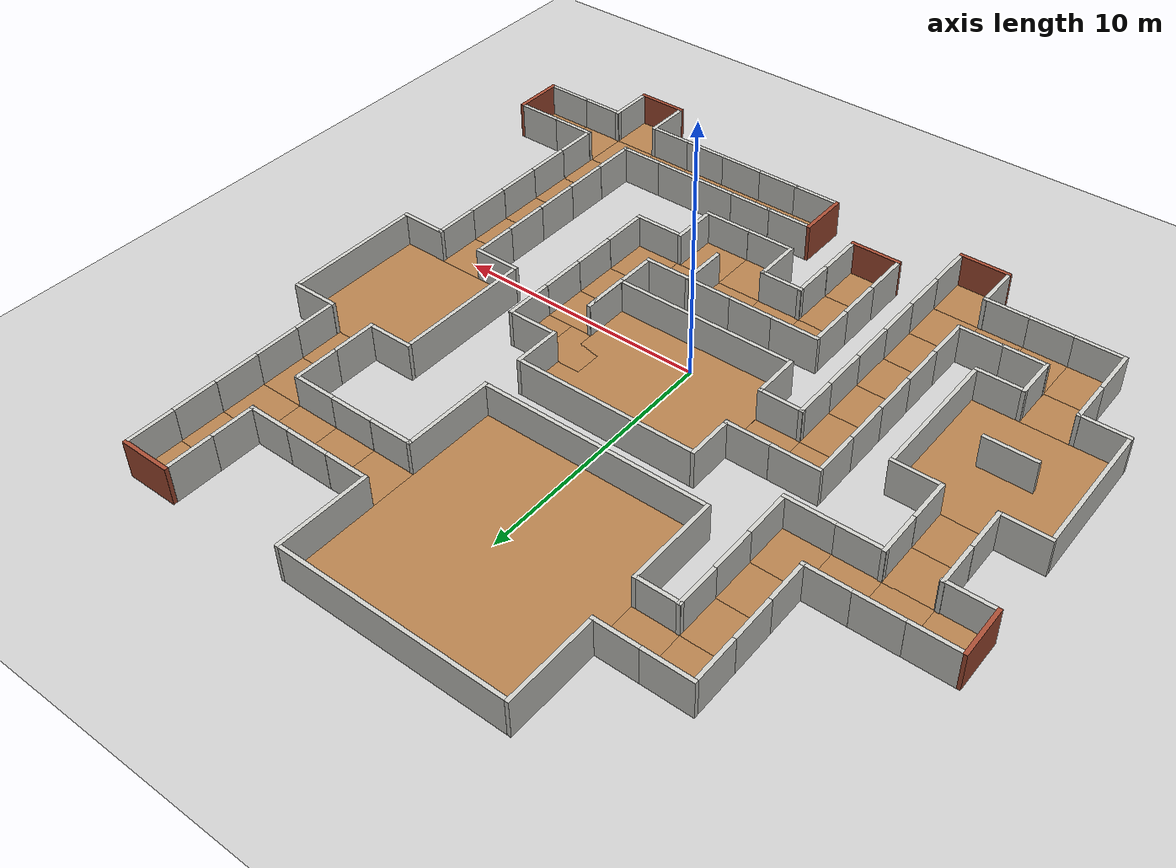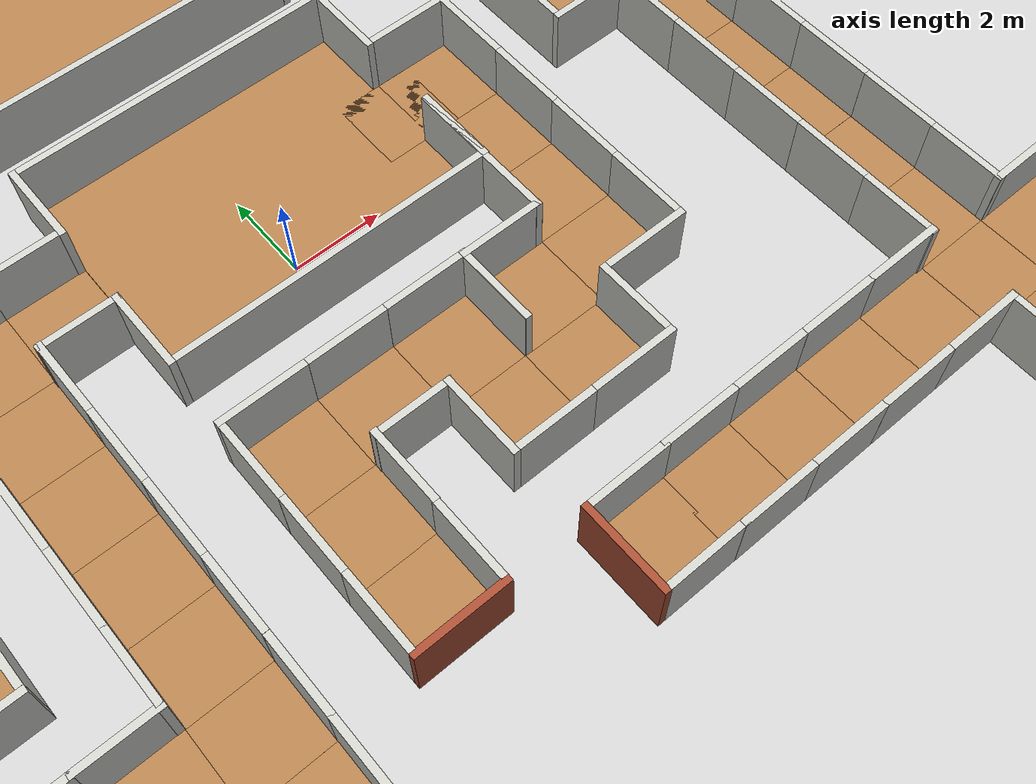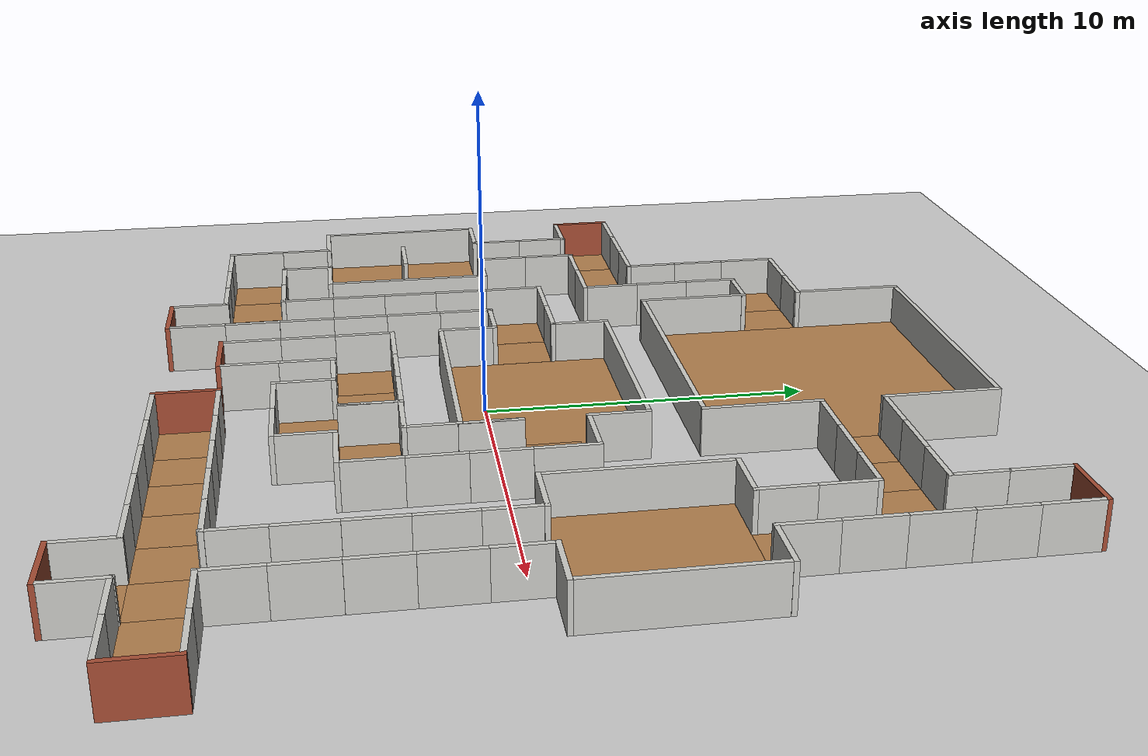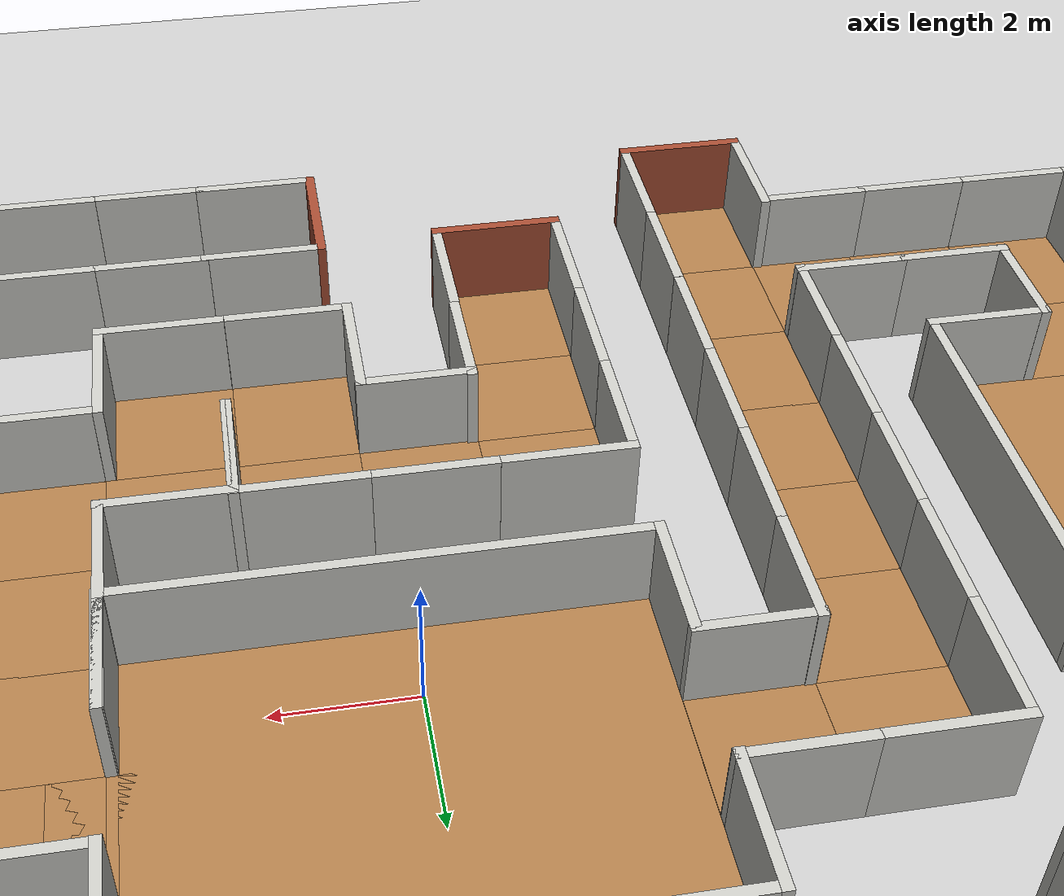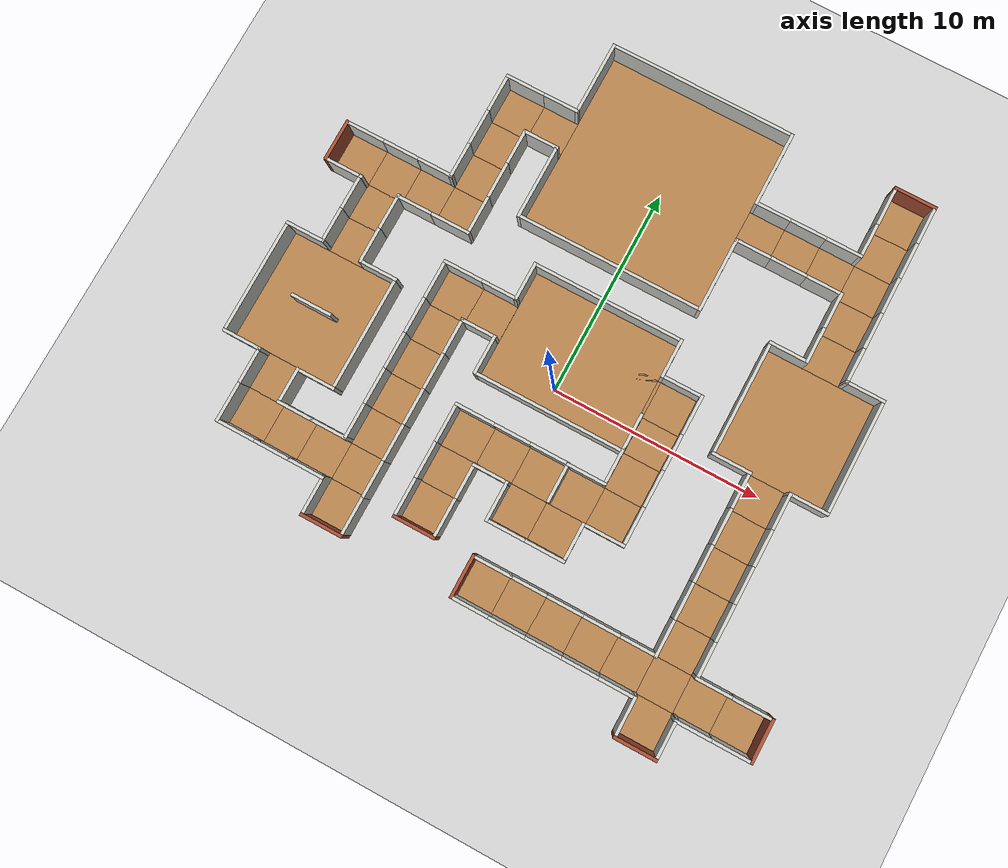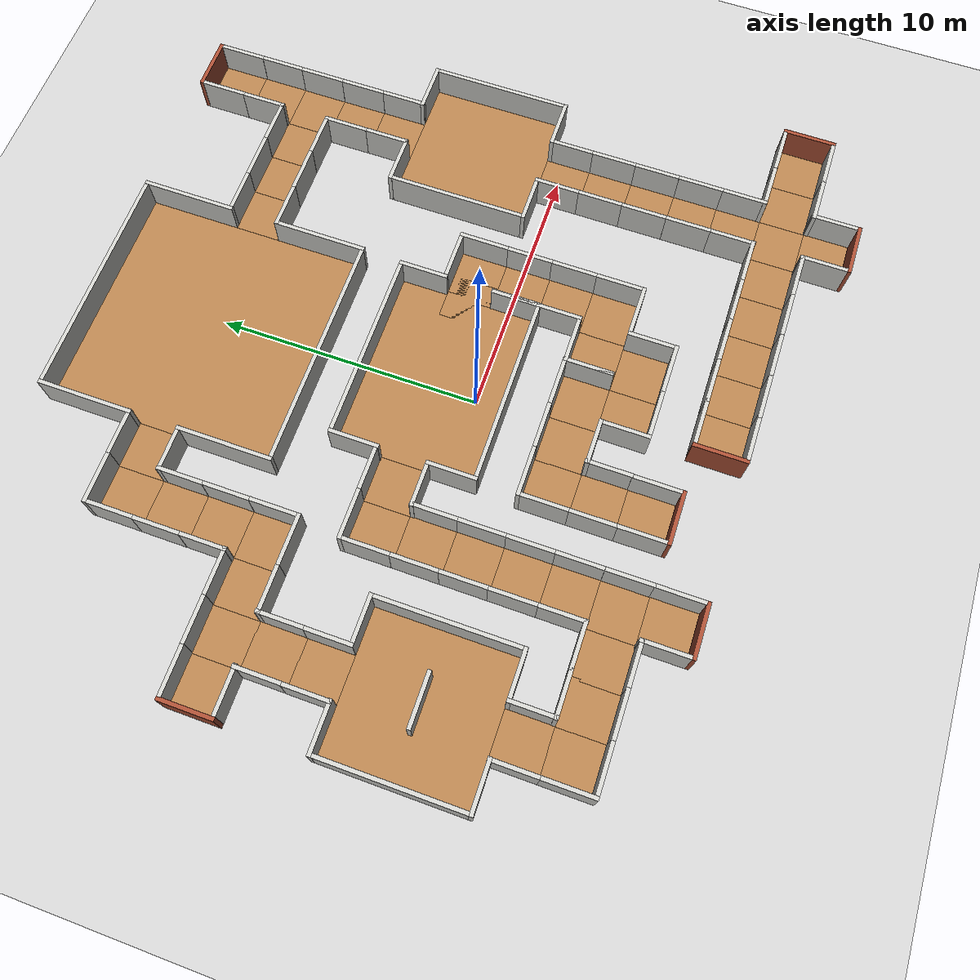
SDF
<sdf version="1.6">
 <world name="default">
  <light name="sun" type="directional">
   <pose>0 0 10 0 -0 0</pose>
   <diffuse>0.8 0.8 0.8 1</diffuse>
   <specular>0.1 0.1 0.1 1</specular>
   <attenuation>
    <range>1000</range>
    <constant>0.9</constant>
    <linear>0.01</linear>
    <quadratic>0.001</quadratic>
   </attenuation>
   <direction>-0.5 0.5 -1</direction>
  </light>
  <model name="ground_plane">
   <static>1</static>
   <link name="link">
    <collision name="collision">
     <geometry><plane><normal>0 0 1</normal><size>100 100</size></plane></geometry>
     <surface><friction><ode><mu>100</mu><mu2>50</mu2></ode></friction></surface>
    </collision>
    <visual name="visual">
     <cast_shadows>0</cast_shadows>
     <geometry><plane><normal>0 0 1</normal><size>100 100</size></plane></geometry>
     <material>
      <script><uri>file://media/materials/scripts/gazebo.material</uri><name>Gazebo/Grey</name></script>
     </material>
    </visual>
   </link>
  </model>
  <gravity>0 0 -9.8</gravity>
  <magnetic_field>6e-06 2.3e-05 -4.2e-05</magnetic_field>
  <atmosphere type="adiabatic"/>
  <physics name="default_physics" default="0" type="ode">
   <max_step_size>0.001</max_step_size>
   <real_time_factor>1</real_time_factor>
   <real_time_update_rate>1000</real_time_update_rate>
  </physics>
  <scene><ambient>0.4 0.4 0.4 1</ambient><background>0.7 0.7 0.7 1</background><shadows>1</shadows></scene>
  <spherical_coordinates>
   <surface_model>EARTH_WGS84</surface_model>
   <latitude_deg>0</latitude_deg>
   <longitude_deg>0</longitude_deg>
   <elevation>0</elevation>
   <heading_deg>0</heading_deg>
  </spherical_coordinates>
  <model name="nerve_end">
   <pose>-2.33142 -7.13266 0 0 0 -3.14159</pose>
   <link name="Wall_0">
    <collision name="Wall_0_Collision">
     <geometry><box><size>1.76 1.75 0.2</size></box></geometry>
     <pose>0 0 0.1 0 -0 0</pose>
    </collision>
    <visual name="Wall_0_Visual">
     <pose>0 0 0.1 0 -0 0</pose>
     <geometry><box><size>1.76 1.75 0.2</size></box></geometry>
     <material>
      <script><uri>file://media/materials/scripts/gazebo.material</uri><name>Gazebo/Wood</name></script>
      <ambient>1 0.764706 0.305882 1</ambient>
     </material>
    </visual>
    <pose>-0.009 -0.064 0 0 -0 0</pose>
   </link>
   <link name="Wall_2">
    <collision name="Wall_2_Collision">
     <geometry><box><size>1.8 0.15 1.5</size></box></geometry>
     <pose>0 0 0.75 0 -0 0</pose>
    </collision>
    <visual name="Wall_2_Visual">
     <pose>0 0 0.75 0 -0 0</pose>
     <geometry><box><size>1.8 0.15 1.5</size></box></geometry>
     <material>
      <script><uri>file://media/materials/scripts/gazebo.material</uri><name>Gazebo/CeilingTiled</name></script>
      <ambient>1 0.764706 0.305882 1</ambient>
     </material>
    </visual>
    <pose>-0.95 -0.065 0 0 0 -1.5708</pose>
   </link>
   <link name="Wall_4">
    <collision name="Wall_4_Collision">
     <geometry><box><size>1.8 0.15 1.5</size></box></geometry>
     <pose>0 0 0.75 0 -0 0</pose>
    </collision>
    <visual name="Wall_4_Visual">
     <pose>0 0 0.75 0 -0 0</pose>
     <geometry><box><size>1.8 0.15 1.5</size></box></geometry>
     <material>
      <script><uri>file://media/materials/scripts/gazebo.material</uri><name>Gazebo/CeilingTiled</name></script>
      <ambient>1 0.764706 0.305882 1</ambient>
     </material>
    </visual>
    <pose>0.95 -0.065 0 0 0 -1.5708</pose>
   </link>
   <link name="Wall_6">
    <collision name="Wall_6_Collision">
     <geometry><box><size>2.05 0.15 1.5</size></box></geometry>
     <pose>0 0 0.75 0 -0 0</pose>
    </collision>
    <visual name="Wall_6_Visual">
     <pose>0 0 0.75 0 -0 0</pose>
     <geometry><box><size>2.05 0.15 1.5</size></box></geometry>
     <material>
      <script><uri>file://media/materials/scripts/gazebo.material</uri><name>Gazebo/Bricks</name></script>
      <ambient>0.996078 0.47451 0.0196078 1</ambient>
     </material>
    </visual>
    <pose>0 0.89 0 0 -0 0</pose>
   </link>
   <static>1</static>
  </model>
  <model name="nerve_straight_4">
   <pose>-2.32642 -5.32807 0 0 -0 0</pose>
   <link name="Wall_0">
    <collision name="Wall_0_Collision">
     <geometry><box><size>1.76 1.75 0.2</size></box></geometry>
     <pose>0 0 0.1 0 -0 0</pose>
    </collision>
    <visual name="Wall_0_Visual">
     <pose>0 0 0.1 0 -0 0</pose>
     <geometry><box><size>1.76 1.75 0.2</size></box></geometry>
     <material>
      <script><uri>file://media/materials/scripts/gazebo.material</uri><name>Gazebo/Wood</name></script>
      <ambient>1 0.764706 0.305882 1</ambient>
     </material>
    </visual>
    <pose>0.005 -0.002 0 0 -0 3.14159</pose>
   </link>
   <link name="Wall_2">
    <collision name="Wall_2_Collision">
     <geometry><box><size>1.75 0.15 1.5</size></box></geometry>
     <pose>0 0 0.75 0 -0 0</pose>
    </collision>
    <visual name="Wall_2_Visual">
     <pose>0 0 0.75 0 -0 0</pose>
     <geometry><box><size>1.75 0.15 1.5</size></box></geometry>
     <material>
      <script><uri>file://media/materials/scripts/gazebo.material</uri><name>Gazebo/CeilingTiled</name></script>
      <ambient>1 0.764706 0.305882 1</ambient>
     </material>
    </visual>
    <pose>-0.955 0.002 0 0 0 -1.5708</pose>
   </link>
   <link name="Wall_4">
    <collision name="Wall_4_Collision">
     <geometry><box><size>1.75 0.15 1.5</size></box></geometry>
     <pose>0 0 0.75 0 -0 0</pose>
    </collision>
    <visual name="Wall_4_Visual">
     <pose>0 0 0.75 0 -0 0</pose>
     <geometry><box><size>1.75 0.15 1.5</size></box></geometry>
     <material>
      <script><uri>file://media/materials/scripts/gazebo.material</uri><name>Gazebo/CeilingTiled</name></script>
      <ambient>1 0.764706 0.305882 1</ambient>
     </material>
    </visual>
    <pose>0.955 0.002 0 0 0 -1.5708</pose>
   </link>
   <static>1</static>
  </model>
  <model name="nerve_corner_4">
   <pose>-2.40033 -3.51919 0 0 -0 0</pose>
   <link name="Wall_0">
    <collision name="Wall_0_Collision">
     <geometry><box><size>1.76 1.75 0.2</size></box></geometry>
     <pose>0 0 0.1 0 -0 0</pose>
    </collision>
    <visual name="Wall_0_Visual">
     <pose>0 0 0.1 0 -0 0</pose>
     <geometry><box><size>1.76 1.75 0.2</size></box></geometry>
     <material>
      <script><uri>file://media/materials/scripts/gazebo.material</uri><name>Gazebo/Wood</name></script>
      <ambient>1 0.764706 0.305882 1</ambient>
     </material>
    </visual>
    <pose>0.077507 -0.077007 0 0 -0 3.14159</pose>
   </link>
   <link name="Wall_2">
    <collision name="Wall_2_Collision">
     <geometry><box><size>1.75 0.15 1.5</size></box></geometry>
     <pose>0 0 0.75 0 -0 0</pose>
    </collision>
    <visual name="Wall_2_Visual">
     <pose>0 0 0.75 0 -0 0</pose>
     <geometry><box><size>1.75 0.15 1.5</size></box></geometry>
     <material>
      <script><uri>file://media/materials/scripts/gazebo.material</uri><name>Gazebo/CeilingTiled</name></script>
      <ambient>1 0.764706 0.305882 1</ambient>
     </material>
    </visual>
    <pose>-0.882493 -0.073007 0 0 0 -1.5708</pose>
   </link>
   <link name="Wall_4">
    <collision name="Wall_4_Collision">
     <geometry><box><size>1.91042 0.15 1.5</size></box></geometry>
     <pose>0 0 0.75 0 -0 0</pose>
    </collision>
    <visual name="Wall_4_Visual">
     <pose>0 0 0.75 0 -0 0</pose>
     <geometry><box><size>1.91042 0.15 1.5</size></box></geometry>
     <material>
      <script><uri>file://media/materials/scripts/gazebo.material</uri><name>Gazebo/CeilingTiled</name></script>
      <ambient>1 0.764706 0.305882 1</ambient>
     </material>
    </visual>
    <pose>-0.002284 0.876825 0 0 -0 3.1414</pose>
   </link>
   <static>1</static>
  </model>
  <model name="nerve_straight_7">
   <pose>-0.5793 -3.59925 0 0 0 -1.5708</pose>
   <link name="Wall_0">
    <collision name="Wall_0_Collision">
     <geometry><box><size>1.76 1.75 0.2</size></box></geometry>
     <pose>0 0 0.1 0 -0 0</pose>
    </collision>
    <visual name="Wall_0_Visual">
     <pose>0 0 0.1 0 -0 0</pose>
     <geometry><box><size>1.76 1.75 0.2</size></box></geometry>
     <material>
      <script><uri>file://media/materials/scripts/gazebo.material</uri><name>Gazebo/Wood</name></script>
      <ambient>1 0.764706 0.305882 1</ambient>
     </material>
    </visual>
    <pose>0.005 -0.002 0 0 -0 3.14159</pose>
   </link>
   <link name="Wall_2">
    <collision name="Wall_2_Collision">
     <geometry><box><size>1.75 0.15 1.5</size></box></geometry>
     <pose>0 0 0.75 0 -0 0</pose>
    </collision>
    <visual name="Wall_2_Visual">
     <pose>0 0 0.75 0 -0 0</pose>
     <geometry><box><size>1.75 0.15 1.5</size></box></geometry>
     <material>
      <script><uri>file://media/materials/scripts/gazebo.material</uri><name>Gazebo/CeilingTiled</name></script>
      <ambient>1 0.764706 0.305882 1</ambient>
     </material>
    </visual>
    <pose>-0.955 0.002 0 0 0 -1.5708</pose>
   </link>
   <link name="Wall_4">
    <collision name="Wall_4_Collision">
     <geometry><box><size>1.75 0.15 1.5</size></box></geometry>
     <pose>0 0 0.75 0 -0 0</pose>
    </collision>
    <visual name="Wall_4_Visual">
     <pose>0 0 0.75 0 -0 0</pose>
     <geometry><box><size>1.75 0.15 1.5</size></box></geometry>
     <material>
      <script><uri>file://media/materials/scripts/gazebo.material</uri><name>Gazebo/CeilingTiled</name></script>
      <ambient>1 0.764706 0.305882 1</ambient>
     </material>
    </visual>
    <pose>0.955 0.002 0 0 0 -1.5708</pose>
   </link>
   <static>1</static>
  </model>
  <model name="nerve_corner_5">
   <pose>1.24131 -3.5279 0 0 0 -1.5708</pose>
   <link name="Wall_0">
    <collision name="Wall_0_Collision">
     <geometry><box><size>1.76 1.75 0.2</size></box></geometry>
     <pose>0 0 0.1 0 -0 0</pose>
    </collision>
    <visual name="Wall_0_Visual">
     <pose>0 0 0.1 0 -0 0</pose>
     <geometry><box><size>1.76 1.75 0.2</size></box></geometry>
     <material>
      <script><uri>file://media/materials/scripts/gazebo.material</uri><name>Gazebo/Wood</name></script>
      <ambient>1 0.764706 0.305882 1</ambient>
     </material>
    </visual>
    <pose>0.077507 -0.077007 0 0 -0 3.14159</pose>
   </link>
   <link name="Wall_2">
    <collision name="Wall_2_Collision">
     <geometry><box><size>1.75 0.15 1.5</size></box></geometry>
     <pose>0 0 0.75 0 -0 0</pose>
    </collision>
    <visual name="Wall_2_Visual">
     <pose>0 0 0.75 0 -0 0</pose>
     <geometry><box><size>1.75 0.15 1.5</size></box></geometry>
     <material>
      <script><uri>file://media/materials/scripts/gazebo.material</uri><name>Gazebo/CeilingTiled</name></script>
      <ambient>1 0.764706 0.305882 1</ambient>
     </material>
    </visual>
    <pose>-0.882493 -0.073007 0 0 0 -1.5708</pose>
   </link>
   <link name="Wall_4">
    <collision name="Wall_4_Collision">
     <geometry><box><size>1.91042 0.15 1.5</size></box></geometry>
     <pose>0 0 0.75 0 -0 0</pose>
    </collision>
    <visual name="Wall_4_Visual">
     <pose>0 0 0.75 0 -0 0</pose>
     <geometry><box><size>1.91042 0.15 1.5</size></box></geometry>
     <material>
      <script><uri>file://media/materials/scripts/gazebo.material</uri><name>Gazebo/CeilingTiled</name></script>
      <ambient>1 0.764706 0.305882 1</ambient>
     </material>
    </visual>
    <pose>-0.002284 0.876825 0 0 -0 3.1414</pose>
   </link>
   <static>1</static>
  </model>
  <model name="nerve_corner_6">
   <pose>1.09271 -5.44009 0 0 -0 1.57079</pose>
   <link name="Wall_0">
    <collision name="Wall_0_Collision">
     <geometry><box><size>1.76 1.75 0.2</size></box></geometry>
     <pose>0 0 0.1 0 -0 0</pose>
    </collision>
    <visual name="Wall_0_Visual">
     <pose>0 0 0.1 0 -0 0</pose>
     <geometry><box><size>1.76 1.75 0.2</size></box></geometry>
     <material>
      <script><uri>file://media/materials/scripts/gazebo.material</uri><name>Gazebo/Wood</name></script>
      <ambient>1 0.764706 0.305882 1</ambient>
     </material>
    </visual>
    <pose>0.077507 -0.077007 0 0 -0 3.14159</pose>
   </link>
   <link name="Wall_2">
    <collision name="Wall_2_Collision">
     <geometry><box><size>1.75 0.15 1.5</size></box></geometry>
     <pose>0 0 0.75 0 -0 0</pose>
    </collision>
    <visual name="Wall_2_Visual">
     <pose>0 0 0.75 0 -0 0</pose>
     <geometry><box><size>1.75 0.15 1.5</size></box></geometry>
     <material>
      <script><uri>file://media/materials/scripts/gazebo.material</uri><name>Gazebo/CeilingTiled</name></script>
      <ambient>1 0.764706 0.305882 1</ambient>
     </material>
    </visual>
    <pose>-0.882493 -0.073007 0 0 0 -1.5708</pose>
   </link>
   <link name="Wall_4">
    <collision name="Wall_4_Collision">
     <geometry><box><size>1.91042 0.15 1.5</size></box></geometry>
     <pose>0 0 0.75 0 -0 0</pose>
    </collision>
    <visual name="Wall_4_Visual">
     <pose>0 0 0.75 0 -0 0</pose>
     <geometry><box><size>1.91042 0.15 1.5</size></box></geometry>
     <material>
      <script><uri>file://media/materials/scripts/gazebo.material</uri><name>Gazebo/CeilingTiled</name></script>
      <ambient>1 0.764706 0.305882 1</ambient>
     </material>
    </visual>
    <pose>-0.002284 0.876825 0 0 -0 3.1414</pose>
   </link>
   <static>1</static>
  </model>
  <model name="nerve_corner_7">
   <pose>3.00607 -3.54167 0 0 -0 0</pose>
   <link name="Wall_0">
    <collision name="Wall_0_Collision">
     <geometry><box><size>1.76 1.75 0.2</size></box></geometry>
     <pose>0 0 0.1 0 -0 0</pose>
    </collision>
    <visual name="Wall_0_Visual">
     <pose>0 0 0.1 0 -0 0</pose>
     <geometry><box><size>1.76 1.75 0.2</size></box></geometry>
     <material>
      <script><uri>file://media/materials/scripts/gazebo.material</uri><name>Gazebo/Wood</name></script>
      <ambient>1 0.764706 0.305882 1</ambient>
     </material>
    </visual>
    <pose>0.077507 -0.077007 0 0 -0 3.14159</pose>
   </link>
   <link name="Wall_2">
    <collision name="Wall_2_Collision">
     <geometry><box><size>1.75 0.15 1.5</size></box></geometry>
     <pose>0 0 0.75 0 -0 0</pose>
    </collision>
    <visual name="Wall_2_Visual">
     <pose>0 0 0.75 0 -0 0</pose>
     <geometry><box><size>1.75 0.15 1.5</size></box></geometry>
     <material>
      <script><uri>file://media/materials/scripts/gazebo.material</uri><name>Gazebo/CeilingTiled</name></script>
      <ambient>1 0.764706 0.305882 1</ambient>
     </material>
    </visual>
    <pose>-0.882493 -0.073007 0 0 0 -1.5708</pose>
   </link>
   <link name="Wall_4">
    <collision name="Wall_4_Collision">
     <geometry><box><size>1.91042 0.15 1.5</size></box></geometry>
     <pose>0 0 0.75 0 -0 0</pose>
    </collision>
    <visual name="Wall_4_Visual">
     <pose>0 0 0.75 0 -0 0</pose>
     <geometry><box><size>1.91042 0.15 1.5</size></box></geometry>
     <material>
      <script><uri>file://media/materials/scripts/gazebo.material</uri><name>Gazebo/CeilingTiled</name></script>
      <ambient>1 0.764706 0.305882 1</ambient>
     </material>
    </visual>
    <pose>-0.002284 0.876825 0 0 -0 3.1414</pose>
   </link>
   <static>1</static>
  </model>
  <model name="nerve_corner_8">
   <pose>2.996 -5.44292 0 0 -0 3.14159</pose>
   <link name="Wall_0">
    <collision name="Wall_0_Collision">
     <geometry><box><size>1.76 1.75 0.2</size></box></geometry>
     <pose>0 0 0.1 0 -0 0</pose>
    </collision>
    <visual name="Wall_0_Visual">
     <pose>0 0 0.1 0 -0 0</pose>
     <geometry><box><size>1.76 1.75 0.2</size></box></geometry>
     <material>
      <script><uri>file://media/materials/scripts/gazebo.material</uri><name>Gazebo/Wood</name></script>
      <ambient>1 0.764706 0.305882 1</ambient>
     </material>
    </visual>
    <pose>0.077507 -0.077007 0 0 -0 3.14159</pose>
   </link>
   <link name="Wall_2">
    <collision name="Wall_2_Collision">
     <geometry><box><size>1.75 0.15 1.5</size></box></geometry>
     <pose>0 0 0.75 0 -0 0</pose>
    </collision>
    <visual name="Wall_2_Visual">
     <pose>0 0 0.75 0 -0 0</pose>
     <geometry><box><size>1.75 0.15 1.5</size></box></geometry>
     <material>
      <script><uri>file://media/materials/scripts/gazebo.material</uri><name>Gazebo/CeilingTiled</name></script>
      <ambient>1 0.764706 0.305882 1</ambient>
     </material>
    </visual>
    <pose>-0.882493 -0.073007 0 0 0 -1.5708</pose>
   </link>
   <link name="Wall_4">
    <collision name="Wall_4_Collision">
     <geometry><box><size>1.91042 0.15 1.5</size></box></geometry>
     <pose>0 0 0.75 0 -0 0</pose>
    </collision>
    <visual name="Wall_4_Visual">
     <pose>0 0 0.75 0 -0 0</pose>
     <geometry><box><size>1.91042 0.15 1.5</size></box></geometry>
     <material>
      <script><uri>file://media/materials/scripts/gazebo.material</uri><name>Gazebo/CeilingTiled</name></script>
      <ambient>1 0.764706 0.305882 1</ambient>
     </material>
    </visual>
    <pose>-0.002284 0.876825 0 0 -0 3.1414</pose>
   </link>
   <static>1</static>
  </model>
  <model name="nerve_corner_8_clone">
   <pose>4.90397 -3.68999 0 0 0 -3.14159</pose>
   <link name="Wall_0">
    <collision name="Wall_0_Collision">
     <geometry><box><size>1.76 1.75 0.2</size></box></geometry>
     <pose>0 0 0.1 0 -0 0</pose>
    </collision>
    <visual name="Wall_0_Visual">
     <pose>0 0 0.1 0 -0 0</pose>
     <geometry><box><size>1.76 1.75 0.2</size></box></geometry>
     <material>
      <script><uri>file://media/materials/scripts/gazebo.material</uri><name>Gazebo/Wood</name></script>
      <ambient>1 0.764706 0.305882 1</ambient>
     </material>
    </visual>
    <pose>0.077507 -0.077007 0 0 -0 3.14159</pose>
   </link>
   <link name="Wall_2">
    <collision name="Wall_2_Collision">
     <geometry><box><size>1.75 0.15 1.5</size></box></geometry>
     <pose>0 0 0.75 0 -0 0</pose>
    </collision>
    <visual name="Wall_2_Visual">
     <pose>0 0 0.75 0 -0 0</pose>
     <geometry><box><size>1.75 0.15 1.5</size></box></geometry>
     <material>
      <script><uri>file://media/materials/scripts/gazebo.material</uri><name>Gazebo/CeilingTiled</name></script>
      <ambient>1 0.764706 0.305882 1</ambient>
     </material>
    </visual>
    <pose>-0.882493 -0.073007 0 0 0 -1.5708</pose>
   </link>
   <link name="Wall_4">
    <collision name="Wall_4_Collision">
     <geometry><box><size>1.91042 0.15 1.5</size></box></geometry>
     <pose>0 0 0.75 0 -0 0</pose>
    </collision>
    <visual name="Wall_4_Visual">
     <pose>0 0 0.75 0 -0 0</pose>
     <geometry><box><size>1.91042 0.15 1.5</size></box></geometry>
     <material>
      <script><uri>file://media/materials/scripts/gazebo.material</uri><name>Gazebo/CeilingTiled</name></script>
      <ambient>1 0.764706 0.305882 1</ambient>
     </material>
    </visual>
    <pose>-0.002284 0.876825 0 0 -0 3.1414</pose>
   </link>
   <static>1</static>
  </model>
  <model name="nerve_straight_8">
   <pose>4.83321 -1.87129 0 0 -0 0</pose>
   <link name="Wall_0">
    <collision name="Wall_0_Collision">
     <geometry><box><size>1.76 1.75 0.2</size></box></geometry>
     <pose>0 0 0.1 0 -0 0</pose>
    </collision>
    <visual name="Wall_0_Visual">
     <pose>0 0 0.1 0 -0 0</pose>
     <geometry><box><size>1.76 1.75 0.2</size></box></geometry>
     <material>
      <script><uri>file://media/materials/scripts/gazebo.material</uri><name>Gazebo/Wood</name></script>
      <ambient>1 0.764706 0.305882 1</ambient>
     </material>
    </visual>
    <pose>0.005 -0.002 0 0 -0 3.14159</pose>
   </link>
   <link name="Wall_2">
    <collision name="Wall_2_Collision">
     <geometry><box><size>1.75 0.15 1.5</size></box></geometry>
     <pose>0 0 0.75 0 -0 0</pose>
    </collision>
    <visual name="Wall_2_Visual">
     <pose>0 0 0.75 0 -0 0</pose>
     <geometry><box><size>1.75 0.15 1.5</size></box></geometry>
     <material>
      <script><uri>file://media/materials/scripts/gazebo.material</uri><name>Gazebo/CeilingTiled</name></script>
      <ambient>1 0.764706 0.305882 1</ambient>
     </material>
    </visual>
    <pose>-0.955 0.002 0 0 0 -1.5708</pose>
   </link>
   <link name="Wall_4">
    <collision name="Wall_4_Collision">
     <geometry><box><size>1.75 0.15 1.5</size></box></geometry>
     <pose>0 0 0.75 0 -0 0</pose>
    </collision>
    <visual name="Wall_4_Visual">
     <pose>0 0 0.75 0 -0 0</pose>
     <geometry><box><size>1.75 0.15 1.5</size></box></geometry>
     <material>
      <script><uri>file://media/materials/scripts/gazebo.material</uri><name>Gazebo/CeilingTiled</name></script>
      <ambient>1 0.764706 0.305882 1</ambient>
     </material>
    </visual>
    <pose>0.955 0.002 0 0 0 -1.5708</pose>
   </link>
   <static>1</static>
  </model>
  <model name="nerve_straight_8_clone">
   <pose>4.83651 -0.139064 0 0 -0 0</pose>
   <link name="Wall_0">
    <collision name="Wall_0_Collision">
     <geometry><box><size>1.76 1.75 0.2</size></box></geometry>
     <pose>0 0 0.1 0 -0 0</pose>
    </collision>
    <visual name="Wall_0_Visual">
     <pose>0 0 0.1 0 -0 0</pose>
     <geometry><box><size>1.76 1.75 0.2</size></box></geometry>
     <material>
      <script><uri>file://media/materials/scripts/gazebo.material</uri><name>Gazebo/Wood</name></script>
      <ambient>1 0.764706 0.305882 1</ambient>
     </material>
    </visual>
    <pose>0.005 -0.002 0 0 -0 3.14159</pose>
   </link>
   <link name="Wall_2">
    <collision name="Wall_2_Collision">
     <geometry><box><size>1.75 0.15 1.5</size></box></geometry>
     <pose>0 0 0.75 0 -0 0</pose>
    </collision>
    <visual name="Wall_2_Visual">
     <pose>0 0 0.75 0 -0 0</pose>
     <geometry><box><size>1.75 0.15 1.5</size></box></geometry>
     <material>
      <script><uri>file://media/materials/scripts/gazebo.material</uri><name>Gazebo/CeilingTiled</name></script>
      <ambient>1 0.764706 0.305882 1</ambient>
     </material>
    </visual>
    <pose>-0.955 0.002 0 0 0 -1.5708</pose>
   </link>
   <link name="Wall_4">
    <collision name="Wall_4_Collision">
     <geometry><box><size>1.75 0.15 1.5</size></box></geometry>
     <pose>0 0 0.75 0 -0 0</pose>
    </collision>
    <visual name="Wall_4_Visual">
     <pose>0 0 0.75 0 -0 0</pose>
     <geometry><box><size>1.75 0.15 1.5</size></box></geometry>
     <material>
      <script><uri>file://media/materials/scripts/gazebo.material</uri><name>Gazebo/CeilingTiled</name></script>
      <ambient>1 0.764706 0.305882 1</ambient>
     </material>
    </visual>
    <pose>0.955 0.002 0 0 0 -1.5708</pose>
   </link>
   <static>1</static>
  </model>
  <model name="nerve_corner_5_clone">
   <pose>4.91717 1.68936 0 0 0 -1.5708</pose>
   <link name="Wall_0">
    <collision name="Wall_0_Collision">
     <geometry><box><size>1.76 1.75 0.2</size></box></geometry>
     <pose>0 0 0.1 0 -0 0</pose>
    </collision>
    <visual name="Wall_0_Visual">
     <pose>0 0 0.1 0 -0 0</pose>
     <geometry><box><size>1.76 1.75 0.2</size></box></geometry>
     <material>
      <script><uri>file://media/materials/scripts/gazebo.material</uri><name>Gazebo/Wood</name></script>
      <ambient>1 0.764706 0.305882 1</ambient>
     </material>
    </visual>
    <pose>0.077507 -0.077007 0 0 -0 3.14159</pose>
   </link>
   <link name="Wall_2">
    <collision name="Wall_2_Collision">
     <geometry><box><size>1.75 0.15 1.5</size></box></geometry>
     <pose>0 0 0.75 0 -0 0</pose>
    </collision>
    <visual name="Wall_2_Visual">
     <pose>0 0 0.75 0 -0 0</pose>
     <geometry><box><size>1.75 0.15 1.5</size></box></geometry>
     <material>
      <script><uri>file://media/materials/scripts/gazebo.material</uri><name>Gazebo/CeilingTiled</name></script>
      <ambient>1 0.764706 0.305882 1</ambient>
     </material>
    </visual>
    <pose>-0.882493 -0.073007 0 0 0 -1.5708</pose>
   </link>
   <link name="Wall_4">
    <collision name="Wall_4_Collision">
     <geometry><box><size>1.91042 0.15 1.5</size></box></geometry>
     <pose>0 0 0.75 0 -0 0</pose>
    </collision>
    <visual name="Wall_4_Visual">
     <pose>0 0 0.75 0 -0 0</pose>
     <geometry><box><size>1.91042 0.15 1.5</size></box></geometry>
     <material>
      <script><uri>file://media/materials/scripts/gazebo.material</uri><name>Gazebo/CeilingTiled</name></script>
      <ambient>1 0.764706 0.305882 1</ambient>
     </material>
    </visual>
    <pose>-0.002284 0.876825 0 0 -0 3.1414</pose>
   </link>
   <static>1</static>
  </model>
  <model name="nerve_room_3x4">
   <pose>0.322043 1.61667 0 0 0 -1.57079</pose>
   <link name="Wall_11">
    <collision name="Wall_11_Collision">
     <geometry><box><size>7 0.15 1.5</size></box></geometry>
     <pose>0 0 0.75 0 -0 0</pose>
    </collision>
    <visual name="Wall_11_Visual">
     <pose>0 0 0.75 0 -0 0</pose>
     <geometry><box><size>7 0.15 1.5</size></box></geometry>
     <material>
      <script><uri>file://media/materials/scripts/gazebo.material</uri><name>Gazebo/CeilingTiled</name></script>
      <ambient>1 0.764706 0.305882 1</ambient>
     </material>
    </visual>
    <pose>-2.69862 -0.000423 0 0 0 -1.5708</pose>
   </link>
   <link name="Wall_13">
    <collision name="Wall_13_Collision">
     <geometry><box><size>7 0.15 1.5</size></box></geometry>
     <pose>0 0 0.75 0 -0 0</pose>
    </collision>
    <visual name="Wall_13_Visual">
     <pose>0 0 0.75 0 -0 0</pose>
     <geometry><box><size>7 0.15 1.5</size></box></geometry>
     <material>
      <script><uri>file://media/materials/scripts/gazebo.material</uri><name>Gazebo/CeilingTiled</name></script>
      <ambient>1 0.764706 0.305882 1</ambient>
     </material>
    </visual>
    <pose>2.69862 -0.000308 0 0 0 -1.5708</pose>
   </link>
   <link name="Wall_15">
    <collision name="Wall_15_Collision">
     <geometry><box><size>1.9 0.15 1.5</size></box></geometry>
     <pose>0 0 0.75 0 -0 0</pose>
    </collision>
    <visual name="Wall_15_Visual">
     <pose>0 0 0.75 0 -0 0</pose>
     <geometry><box><size>1.9 0.15 1.5</size></box></geometry>
     <material>
      <script><uri>file://media/materials/scripts/gazebo.material</uri><name>Gazebo/CeilingTiled</name></script>
      <ambient>1 0.764706 0.305882 1</ambient>
     </material>
    </visual>
    <pose>-1.82276 -3.57547 0 0 -0 0</pose>
   </link>
   <link name="Wall_17">
    <collision name="Wall_17_Collision">
     <geometry><box><size>1.9 0.15 1.5</size></box></geometry>
     <pose>0 0 0.75 0 -0 0</pose>
    </collision>
    <visual name="Wall_17_Visual">
     <pose>0 0 0.75 0 -0 0</pose>
     <geometry><box><size>1.9 0.15 1.5</size></box></geometry>
     <material>
      <script><uri>file://media/materials/scripts/gazebo.material</uri><name>Gazebo/CeilingTiled</name></script>
      <ambient>1 0.764706 0.305882 1</ambient>
     </material>
    </visual>
    <pose>-1.82217 3.57448 0 0 -0 0</pose>
   </link>
   <link name="Wall_19">
    <collision name="Wall_19_Collision">
     <geometry><box><size>1.9 0.15 1.5</size></box></geometry>
     <pose>0 0 0.75 0 -0 0</pose>
    </collision>
    <visual name="Wall_19_Visual">
     <pose>0 0 0.75 0 -0 0</pose>
     <geometry><box><size>1.9 0.15 1.5</size></box></geometry>
     <material>
      <script><uri>file://media/materials/scripts/gazebo.material</uri><name>Gazebo/CeilingTiled</name></script>
      <ambient>1 0.764706 0.305882 1</ambient>
     </material>
    </visual>
    <pose>1.82197 3.57547 0 0 -0 0</pose>
   </link>
   <link name="Wall_21">
    <collision name="Wall_21_Collision">
     <geometry><box><size>1.9 0.15 1.5</size></box></geometry>
     <pose>0 0 0.75 0 -0 0</pose>
    </collision>
    <visual name="Wall_21_Visual">
     <pose>0 0 0.75 0 -0 0</pose>
     <geometry><box><size>1.9 0.15 1.5</size></box></geometry>
     <material>
      <script><uri>file://media/materials/scripts/gazebo.material</uri><name>Gazebo/CeilingTiled</name></script>
      <ambient>1 0.764706 0.305882 1</ambient>
     </material>
    </visual>
    <pose>1.82281 -3.57503 0 0 -0 0</pose>
   </link>
   <link name="Wall_6">
    <collision name="Wall_6_Collision">
     <geometry><box><size>7 5.25 0.2</size></box></geometry>
     <pose>0 0 0.1 0 -0 0</pose>
    </collision>
    <visual name="Wall_6_Visual">
     <pose>0 0 0.1 0 -0 0</pose>
     <geometry><box><size>7 5.25 0.2</size></box></geometry>
     <material>
      <script><uri>file://media/materials/scripts/gazebo.material</uri><name>Gazebo/Wood</name></script>
      <ambient>1 0.764706 0.305882 1</ambient>
     </material>
    </visual>
    <pose>-0.001169 -0.000255 0 0 -0 1.5708</pose>
   </link>
   <static>1</static>
  </model>
  <model name="nerve_platform_0">
   <pose>3.80884 1.61462 0 0 -0 0</pose>
   <link name="Wall_6">
    <collision name="Wall_6_Collision">
     <geometry><box><size>1.76 1.75 0.2</size></box></geometry>
     <pose>0 0 0.1 0 -0 0</pose>
    </collision>
    <visual name="Wall_6_Visual">
     <pose>0 0 0.1 0 -0 0</pose>
     <geometry><box><size>1.76 1.75 0.2</size></box></geometry>
     <material>
      <script><uri>file://media/materials/scripts/gazebo.material</uri><name>Gazebo/Wood</name></script>
      <ambient>1 0.764706 0.305882 1</ambient>
     </material>
    </visual>
    <pose>0 0 0 0 -0 1.5708</pose>
   </link>
   <static>1</static>
  </model>
  <model name="nerve_straight_9">
   <pose>-4.05488 1.62658 0 0 0 -1.5708</pose>
   <link name="Wall_0">
    <collision name="Wall_0_Collision">
     <geometry><box><size>1.76 1.75 0.2</size></box></geometry>
     <pose>0 0 0.1 0 -0 0</pose>
    </collision>
    <visual name="Wall_0_Visual">
     <pose>0 0 0.1 0 -0 0</pose>
     <geometry><box><size>1.76 1.75 0.2</size></box></geometry>
     <material>
      <script><uri>file://media/materials/scripts/gazebo.material</uri><name>Gazebo/Wood</name></script>
      <ambient>1 0.764706 0.305882 1</ambient>
     </material>
    </visual>
    <pose>0.005 -0.002 0 0 -0 3.14159</pose>
   </link>
   <link name="Wall_2">
    <collision name="Wall_2_Collision">
     <geometry><box><size>1.75 0.15 1.5</size></box></geometry>
     <pose>0 0 0.75 0 -0 0</pose>
    </collision>
    <visual name="Wall_2_Visual">
     <pose>0 0 0.75 0 -0 0</pose>
     <geometry><box><size>1.75 0.15 1.5</size></box></geometry>
     <material>
      <script><uri>file://media/materials/scripts/gazebo.material</uri><name>Gazebo/CeilingTiled</name></script>
      <ambient>1 0.764706 0.305882 1</ambient>
     </material>
    </visual>
    <pose>-0.955 0.002 0 0 0 -1.5708</pose>
   </link>
   <link name="Wall_4">
    <collision name="Wall_4_Collision">
     <geometry><box><size>1.75 0.15 1.5</size></box></geometry>
     <pose>0 0 0.75 0 -0 0</pose>
    </collision>
    <visual name="Wall_4_Visual">
     <pose>0 0 0.75 0 -0 0</pose>
     <geometry><box><size>1.75 0.15 1.5</size></box></geometry>
     <material>
      <script><uri>file://media/materials/scripts/gazebo.material</uri><name>Gazebo/CeilingTiled</name></script>
      <ambient>1 0.764706 0.305882 1</ambient>
     </material>
    </visual>
    <pose>0.955 0.002 0 0 0 -1.5708</pose>
   </link>
   <static>1</static>
  </model>
  <model name="nerve_corner_9">
   <pose>-5.86899 1.703 0 0 -0 0</pose>
   <link name="Wall_0">
    <collision name="Wall_0_Collision">
     <geometry><box><size>1.76 1.75 0.2</size></box></geometry>
     <pose>0 0 0.1 0 -0 0</pose>
    </collision>
    <visual name="Wall_0_Visual">
     <pose>0 0 0.1 0 -0 0</pose>
     <geometry><box><size>1.76 1.75 0.2</size></box></geometry>
     <material>
      <script><uri>file://media/materials/scripts/gazebo.material</uri><name>Gazebo/Wood</name></script>
      <ambient>1 0.764706 0.305882 1</ambient>
     </material>
    </visual>
    <pose>0.077507 -0.077007 0 0 -0 3.14159</pose>
   </link>
   <link name="Wall_2">
    <collision name="Wall_2_Collision">
     <geometry><box><size>1.75 0.15 1.5</size></box></geometry>
     <pose>0 0 0.75 0 -0 0</pose>
    </collision>
    <visual name="Wall_2_Visual">
     <pose>0 0 0.75 0 -0 0</pose>
     <geometry><box><size>1.75 0.15 1.5</size></box></geometry>
     <material>
      <script><uri>file://media/materials/scripts/gazebo.material</uri><name>Gazebo/CeilingTiled</name></script>
      <ambient>1 0.764706 0.305882 1</ambient>
     </material>
    </visual>
    <pose>-0.882493 -0.073007 0 0 0 -1.5708</pose>
   </link>
   <link name="Wall_4">
    <collision name="Wall_4_Collision">
     <geometry><box><size>1.91042 0.15 1.5</size></box></geometry>
     <pose>0 0 0.75 0 -0 0</pose>
    </collision>
    <visual name="Wall_4_Visual">
     <pose>0 0 0.75 0 -0 0</pose>
     <geometry><box><size>1.91042 0.15 1.5</size></box></geometry>
     <material>
      <script><uri>file://media/materials/scripts/gazebo.material</uri><name>Gazebo/CeilingTiled</name></script>
      <ambient>1 0.764706 0.305882 1</ambient>
     </material>
    </visual>
    <pose>-0.002284 0.876825 0 0 -0 3.1414</pose>
   </link>
   <static>1</static>
  </model>
  <model name="nerve_straight_10">
   <pose>-5.79649 -0.117781 0 0 -0 0</pose>
   <link name="Wall_0">
    <collision name="Wall_0_Collision">
     <geometry><box><size>1.76 1.75 0.2</size></box></geometry>
     <pose>0 0 0.1 0 -0 0</pose>
    </collision>
    <visual name="Wall_0_Visual">
     <pose>0 0 0.1 0 -0 0</pose>
     <geometry><box><size>1.76 1.75 0.2</size></box></geometry>
     <material>
      <script><uri>file://media/materials/scripts/gazebo.material</uri><name>Gazebo/Wood</name></script>
      <ambient>1 0.764706 0.305882 1</ambient>
     </material>
    </visual>
    <pose>0.005 -0.002 0 0 -0 3.14159</pose>
   </link>
   <link name="Wall_2">
    <collision name="Wall_2_Collision">
     <geometry><box><size>1.75 0.15 1.5</size></box></geometry>
     <pose>0 0 0.75 0 -0 0</pose>
    </collision>
    <visual name="Wall_2_Visual">
     <pose>0 0 0.75 0 -0 0</pose>
     <geometry><box><size>1.75 0.15 1.5</size></box></geometry>
     <material>
      <script><uri>file://media/materials/scripts/gazebo.material</uri><name>Gazebo/CeilingTiled</name></script>
      <ambient>1 0.764706 0.305882 1</ambient>
     </material>
    </visual>
    <pose>-0.955 0.002 0 0 0 -1.5708</pose>
   </link>
   <link name="Wall_4">
    <collision name="Wall_4_Collision">
     <geometry><box><size>1.75 0.15 1.5</size></box></geometry>
     <pose>0 0 0.75 0 -0 0</pose>
    </collision>
    <visual name="Wall_4_Visual">
     <pose>0 0 0.75 0 -0 0</pose>
     <geometry><box><size>1.75 0.15 1.5</size></box></geometry>
     <material>
      <script><uri>file://media/materials/scripts/gazebo.material</uri><name>Gazebo/CeilingTiled</name></script>
      <ambient>1 0.764706 0.305882 1</ambient>
     </material>
    </visual>
    <pose>0.955 0.002 0 0 0 -1.5708</pose>
   </link>
   <static>1</static>
  </model>
  <model name="nerve_straight_10_clone">
   <pose>-5.79649 -1.8585 0 0 -0 0</pose>
   <link name="Wall_0">
    <collision name="Wall_0_Collision">
     <geometry><box><size>1.76 1.75 0.2</size></box></geometry>
     <pose>0 0 0.1 0 -0 0</pose>
    </collision>
    <visual name="Wall_0_Visual">
     <pose>0 0 0.1 0 -0 0</pose>
     <geometry><box><size>1.76 1.75 0.2</size></box></geometry>
     <material>
      <script><uri>file://media/materials/scripts/gazebo.material</uri><name>Gazebo/Wood</name></script>
      <ambient>1 0.764706 0.305882 1</ambient>
     </material>
    </visual>
    <pose>0.005 -0.002 0 0 -0 3.14159</pose>
   </link>
   <link name="Wall_2">
    <collision name="Wall_2_Collision">
     <geometry><box><size>1.75 0.15 1.5</size></box></geometry>
     <pose>0 0 0.75 0 -0 0</pose>
    </collision>
    <visual name="Wall_2_Visual">
     <pose>0 0 0.75 0 -0 0</pose>
     <geometry><box><size>1.75 0.15 1.5</size></box></geometry>
     <material>
      <script><uri>file://media/materials/scripts/gazebo.material</uri><name>Gazebo/CeilingTiled</name></script>
      <ambient>1 0.764706 0.305882 1</ambient>
     </material>
    </visual>
    <pose>-0.955 0.002 0 0 0 -1.5708</pose>
   </link>
   <link name="Wall_4">
    <collision name="Wall_4_Collision">
     <geometry><box><size>1.75 0.15 1.5</size></box></geometry>
     <pose>0 0 0.75 0 -0 0</pose>
    </collision>
    <visual name="Wall_4_Visual">
     <pose>0 0 0.75 0 -0 0</pose>
     <geometry><box><size>1.75 0.15 1.5</size></box></geometry>
     <material>
      <script><uri>file://media/materials/scripts/gazebo.material</uri><name>Gazebo/CeilingTiled</name></script>
      <ambient>1 0.764706 0.305882 1</ambient>
     </material>
    </visual>
    <pose>0.955 0.002 0 0 0 -1.5708</pose>
   </link>
   <static>1</static>
  </model>
  <model name="nerve_straight_10_clone_0">
   <pose>-5.79649 -3.60725 0 0 -0 0</pose>
   <link name="Wall_0">
    <collision name="Wall_0_Collision">
     <geometry><box><size>1.76 1.75 0.2</size></box></geometry>
     <pose>0 0 0.1 0 -0 0</pose>
    </collision>
    <visual name="Wall_0_Visual">
     <pose>0 0 0.1 0 -0 0</pose>
     <geometry><box><size>1.76 1.75 0.2</size></box></geometry>
     <material>
      <script><uri>file://media/materials/scripts/gazebo.material</uri><name>Gazebo/Wood</name></script>
      <ambient>1 0.764706 0.305882 1</ambient>
     </material>
    </visual>
    <pose>0.005 -0.002 0 0 -0 3.14159</pose>
   </link>
   <link name="Wall_2">
    <collision name="Wall_2_Collision">
     <geometry><box><size>1.75 0.15 1.5</size></box></geometry>
     <pose>0 0 0.75 0 -0 0</pose>
    </collision>
    <visual name="Wall_2_Visual">
     <pose>0 0 0.75 0 -0 0</pose>
     <geometry><box><size>1.75 0.15 1.5</size></box></geometry>
     <material>
      <script><uri>file://media/materials/scripts/gazebo.material</uri><name>Gazebo/CeilingTiled</name></script>
      <ambient>1 0.764706 0.305882 1</ambient>
     </material>
    </visual>
    <pose>-0.955 0.002 0 0 0 -1.5708</pose>
   </link>
   <link name="Wall_4">
    <collision name="Wall_4_Collision">
     <geometry><box><size>1.75 0.15 1.5</size></box></geometry>
     <pose>0 0 0.75 0 -0 0</pose>
    </collision>
    <visual name="Wall_4_Visual">
     <pose>0 0 0.75 0 -0 0</pose>
     <geometry><box><size>1.75 0.15 1.5</size></box></geometry>
     <material>
      <script><uri>file://media/materials/scripts/gazebo.material</uri><name>Gazebo/CeilingTiled</name></script>
      <ambient>1 0.764706 0.305882 1</ambient>
     </material>
    </visual>
    <pose>0.955 0.002 0 0 0 -1.5708</pose>
   </link>
   <static>1</static>
  </model>
  <model name="nerve_straight_10_clone_1">
   <pose>-5.79649 -5.34509 0 0 -0 0</pose>
   <link name="Wall_0">
    <collision name="Wall_0_Collision">
     <geometry><box><size>1.76 1.75 0.2</size></box></geometry>
     <pose>0 0 0.1 0 -0 0</pose>
    </collision>
    <visual name="Wall_0_Visual">
     <pose>0 0 0.1 0 -0 0</pose>
     <geometry><box><size>1.76 1.75 0.2</size></box></geometry>
     <material>
      <script><uri>file://media/materials/scripts/gazebo.material</uri><name>Gazebo/Wood</name></script>
      <ambient>1 0.764706 0.305882 1</ambient>
     </material>
    </visual>
    <pose>0.005 -0.002 0 0 -0 3.14159</pose>
   </link>
   <link name="Wall_2">
    <collision name="Wall_2_Collision">
     <geometry><box><size>1.75 0.15 1.5</size></box></geometry>
     <pose>0 0 0.75 0 -0 0</pose>
    </collision>
    <visual name="Wall_2_Visual">
     <pose>0 0 0.75 0 -0 0</pose>
     <geometry><box><size>1.75 0.15 1.5</size></box></geometry>
     <material>
      <script><uri>file://media/materials/scripts/gazebo.material</uri><name>Gazebo/CeilingTiled</name></script>
      <ambient>1 0.764706 0.305882 1</ambient>
     </material>
    </visual>
    <pose>-0.955 0.002 0 0 0 -1.5708</pose>
   </link>
   <link name="Wall_4">
    <collision name="Wall_4_Collision">
     <geometry><box><size>1.75 0.15 1.5</size></box></geometry>
     <pose>0 0 0.75 0 -0 0</pose>
    </collision>
    <visual name="Wall_4_Visual">
     <pose>0 0 0.75 0 -0 0</pose>
     <geometry><box><size>1.75 0.15 1.5</size></box></geometry>
     <material>
      <script><uri>file://media/materials/scripts/gazebo.material</uri><name>Gazebo/CeilingTiled</name></script>
      <ambient>1 0.764706 0.305882 1</ambient>
     </material>
    </visual>
    <pose>0.955 0.002 0 0 0 -1.5708</pose>
   </link>
   <static>1</static>
  </model>
  <model name="nerve_corner_11">
   <pose>-11.0361 -7.16168 0 0 -0 1.57079</pose>
   <link name="Wall_0">
    <collision name="Wall_0_Collision">
     <geometry><box><size>1.76 1.75 0.2</size></box></geometry>
     <pose>0 0 0.1 0 -0 0</pose>
    </collision>
    <visual name="Wall_0_Visual">
     <pose>0 0 0.1 0 -0 0</pose>
     <geometry><box><size>1.76 1.75 0.2</size></box></geometry>
     <material>
      <script><uri>file://media/materials/scripts/gazebo.material</uri><name>Gazebo/Wood</name></script>
      <ambient>1 0.764706 0.305882 1</ambient>
     </material>
    </visual>
    <pose>0.077507 -0.077007 0 0 -0 3.14159</pose>
   </link>
   <link name="Wall_2">
    <collision name="Wall_2_Collision">
     <geometry><box><size>1.75 0.15 1.5</size></box></geometry>
     <pose>0 0 0.75 0 -0 0</pose>
    </collision>
    <visual name="Wall_2_Visual">
     <pose>0 0 0.75 0 -0 0</pose>
     <geometry><box><size>1.75 0.15 1.5</size></box></geometry>
     <material>
      <script><uri>file://media/materials/scripts/gazebo.material</uri><name>Gazebo/CeilingTiled</name></script>
      <ambient>1 0.764706 0.305882 1</ambient>
     </material>
    </visual>
    <pose>-0.882493 -0.073007 0 0 0 -1.5708</pose>
   </link>
   <link name="Wall_4">
    <collision name="Wall_4_Collision">
     <geometry><box><size>1.91042 0.15 1.5</size></box></geometry>
     <pose>0 0 0.75 0 -0 0</pose>
    </collision>
    <visual name="Wall_4_Visual">
     <pose>0 0 0.75 0 -0 0</pose>
     <geometry><box><size>1.91042 0.15 1.5</size></box></geometry>
     <material>
      <script><uri>file://media/materials/scripts/gazebo.material</uri><name>Gazebo/CeilingTiled</name></script>
      <ambient>1 0.764706 0.305882 1</ambient>
     </material>
    </visual>
    <pose>-0.002284 0.876825 0 0 -0 3.1414</pose>
   </link>
   <static>1</static>
  </model>
  <model name="nerve_straight_10_clone_1_clone">
   <pose>-10.9569 -5.3391 0 0 -0 0</pose>
   <link name="Wall_0">
    <collision name="Wall_0_Collision">
     <geometry><box><size>1.76 1.75 0.2</size></box></geometry>
     <pose>0 0 0.1 0 -0 0</pose>
    </collision>
    <visual name="Wall_0_Visual">
     <pose>0 0 0.1 0 -0 0</pose>
     <geometry><box><size>1.76 1.75 0.2</size></box></geometry>
     <material>
      <script><uri>file://media/materials/scripts/gazebo.material</uri><name>Gazebo/Wood</name></script>
      <ambient>1 0.764706 0.305882 1</ambient>
     </material>
    </visual>
    <pose>0.005 -0.002 0 0 -0 3.14159</pose>
   </link>
   <link name="Wall_2">
    <collision name="Wall_2_Collision">
     <geometry><box><size>1.75 0.15 1.5</size></box></geometry>
     <pose>0 0 0.75 0 -0 0</pose>
    </collision>
    <visual name="Wall_2_Visual">
     <pose>0 0 0.75 0 -0 0</pose>
     <geometry><box><size>1.75 0.15 1.5</size></box></geometry>
     <material>
      <script><uri>file://media/materials/scripts/gazebo.material</uri><name>Gazebo/CeilingTiled</name></script>
      <ambient>1 0.764706 0.305882 1</ambient>
     </material>
    </visual>
    <pose>-0.955 0.002 0 0 0 -1.5708</pose>
   </link>
   <link name="Wall_4">
    <collision name="Wall_4_Collision">
     <geometry><box><size>1.75 0.15 1.5</size></box></geometry>
     <pose>0 0 0.75 0 -0 0</pose>
    </collision>
    <visual name="Wall_4_Visual">
     <pose>0 0 0.75 0 -0 0</pose>
     <geometry><box><size>1.75 0.15 1.5</size></box></geometry>
     <material>
      <script><uri>file://media/materials/scripts/gazebo.material</uri><name>Gazebo/CeilingTiled</name></script>
      <ambient>1 0.764706 0.305882 1</ambient>
     </material>
    </visual>
    <pose>0.955 0.002 0 0 0 -1.5708</pose>
   </link>
   <static>1</static>
  </model>
  <model name="nerve_straight_10_clone_1_clone_0">
   <pose>-7.54894 -7.08598 0 0 0 -1.5708</pose>
   <link name="Wall_0">
    <collision name="Wall_0_Collision">
     <geometry><box><size>1.76 1.75 0.2</size></box></geometry>
     <pose>0 0 0.1 0 -0 0</pose>
    </collision>
    <visual name="Wall_0_Visual">
     <pose>0 0 0.1 0 -0 0</pose>
     <geometry><box><size>1.76 1.75 0.2</size></box></geometry>
     <material>
      <script><uri>file://media/materials/scripts/gazebo.material</uri><name>Gazebo/Wood</name></script>
      <ambient>1 0.764706 0.305882 1</ambient>
     </material>
    </visual>
    <pose>0.005 -0.002 0 0 -0 3.14159</pose>
   </link>
   <link name="Wall_2">
    <collision name="Wall_2_Collision">
     <geometry><box><size>1.75 0.15 1.5</size></box></geometry>
     <pose>0 0 0.75 0 -0 0</pose>
    </collision>
    <visual name="Wall_2_Visual">
     <pose>0 0 0.75 0 -0 0</pose>
     <geometry><box><size>1.75 0.15 1.5</size></box></geometry>
     <material>
      <script><uri>file://media/materials/scripts/gazebo.material</uri><name>Gazebo/CeilingTiled</name></script>
      <ambient>1 0.764706 0.305882 1</ambient>
     </material>
    </visual>
    <pose>-0.955 0.002 0 0 0 -1.5708</pose>
   </link>
   <link name="Wall_4">
    <collision name="Wall_4_Collision">
     <geometry><box><size>1.75 0.15 1.5</size></box></geometry>
     <pose>0 0 0.75 0 -0 0</pose>
    </collision>
    <visual name="Wall_4_Visual">
     <pose>0 0 0.75 0 -0 0</pose>
     <geometry><box><size>1.75 0.15 1.5</size></box></geometry>
     <material>
      <script><uri>file://media/materials/scripts/gazebo.material</uri><name>Gazebo/CeilingTiled</name></script>
      <ambient>1 0.764706 0.305882 1</ambient>
     </material>
    </visual>
    <pose>0.955 0.002 0 0 0 -1.5708</pose>
   </link>
   <static>1</static>
  </model>
  <model name="nerve_room_3x3_split">
   <pose>-10.9537 -1.84017 0 0 -0 0</pose>
   <link name="Wall_11">
    <collision name="Wall_11_Collision">
     <geometry><box><size>5.25 0.15 1.5</size></box></geometry>
     <pose>0 0 0.75 0 -0 0</pose>
    </collision>
    <visual name="Wall_11_Visual">
     <pose>0 0 0.75 0 -0 0</pose>
     <geometry><box><size>5.25 0.15 1.5</size></box></geometry>
     <material>
      <script><uri>file://media/materials/scripts/gazebo.material</uri><name>Gazebo/CeilingTiled</name></script>
      <ambient>1 0.764706 0.305882 1</ambient>
     </material>
    </visual>
    <pose>-2.69653 -0.003278 0 0 0 -1.5708</pose>
   </link>
   <link name="Wall_13">
    <collision name="Wall_13_Collision">
     <geometry><box><size>5.25 0.15 1.5</size></box></geometry>
     <pose>0 0 0.75 0 -0 0</pose>
    </collision>
    <visual name="Wall_13_Visual">
     <pose>0 0 0.75 0 -0 0</pose>
     <geometry><box><size>5.25 0.15 1.5</size></box></geometry>
     <material>
      <script><uri>file://media/materials/scripts/gazebo.material</uri><name>Gazebo/CeilingTiled</name></script>
      <ambient>1 0.764706 0.305882 1</ambient>
     </material>
    </visual>
    <pose>2.69688 -0.000452 0 0 0 -1.5708</pose>
   </link>
   <link name="Wall_15">
    <collision name="Wall_15_Collision">
     <geometry><box><size>1.9 0.15 1.5</size></box></geometry>
     <pose>0 0 0.75 0 -0 0</pose>
    </collision>
    <visual name="Wall_15_Visual">
     <pose>0 0 0.75 0 -0 0</pose>
     <geometry><box><size>1.9 0.15 1.5</size></box></geometry>
     <material>
      <script><uri>file://media/materials/scripts/gazebo.material</uri><name>Gazebo/CeilingTiled</name></script>
      <ambient>1 0.764706 0.305882 1</ambient>
     </material>
    </visual>
    <pose>-1.82279 -2.70217 0 0 -0 0</pose>
   </link>
   <link name="Wall_17">
    <collision name="Wall_17_Collision">
     <geometry><box><size>1.9 0.15 1.5</size></box></geometry>
     <pose>0 0 0.75 0 -0 0</pose>
    </collision>
    <visual name="Wall_17_Visual">
     <pose>0 0 0.75 0 -0 0</pose>
     <geometry><box><size>1.9 0.15 1.5</size></box></geometry>
     <material>
      <script><uri>file://media/materials/scripts/gazebo.material</uri><name>Gazebo/CeilingTiled</name></script>
      <ambient>1 0.764706 0.305882 1</ambient>
     </material>
    </visual>
    <pose>-1.82219 2.69878 0 0 -0 0</pose>
   </link>
   <link name="Wall_19">
    <collision name="Wall_19_Collision">
     <geometry><box><size>1.9 0.15 1.5</size></box></geometry>
     <pose>0 0 0.75 0 -0 0</pose>
    </collision>
    <visual name="Wall_19_Visual">
     <pose>0 0 0.75 0 -0 0</pose>
     <geometry><box><size>1.9 0.15 1.5</size></box></geometry>
     <material>
      <script><uri>file://media/materials/scripts/gazebo.material</uri><name>Gazebo/CeilingTiled</name></script>
      <ambient>1 0.764706 0.305882 1</ambient>
     </material>
    </visual>
    <pose>1.82194 2.70217 0 0 -0 0</pose>
   </link>
   <link name="Wall_21">
    <collision name="Wall_21_Collision">
     <geometry><box><size>1.9 0.15 1.5</size></box></geometry>
     <pose>0 0 0.75 0 -0 0</pose>
    </collision>
    <visual name="Wall_21_Visual">
     <pose>0 0 0.75 0 -0 0</pose>
     <geometry><box><size>1.9 0.15 1.5</size></box></geometry>
     <material>
      <script><uri>file://media/materials/scripts/gazebo.material</uri><name>Gazebo/CeilingTiled</name></script>
      <ambient>1 0.764706 0.305882 1</ambient>
     </material>
    </visual>
    <pose>1.82279 -2.70173 0 0 -0 0</pose>
   </link>
   <link name="Wall_23">
    <collision name="Wall_23_Collision">
     <geometry><box><size>2 0.15 1.5</size></box></geometry>
     <pose>0 0 0.75 0 -0 0</pose>
    </collision>
    <visual name="Wall_23_Visual">
     <pose>0 0 0.75 0 -0 0</pose>
     <geometry><box><size>2 0.15 1.5</size></box></geometry>
     <material>
      <script><uri>file://media/materials/scripts/gazebo.material</uri><name>Gazebo/CeilingTiled</name></script>
      <ambient>1 0.764706 0.305882 1</ambient>
     </material>
    </visual>
    <pose>0.033144 0.01482 0 0 -0 0</pose>
   </link>
   <link name="Wall_6">
    <collision name="Wall_6_Collision">
     <geometry><box><size>5.26 5.25 0.2</size></box></geometry>
     <pose>0 0 0.1 0 -0 0</pose>
    </collision>
    <visual name="Wall_6_Visual">
     <pose>0 0 0.1 0 -0 0</pose>
     <geometry><box><size>5.26 5.25 0.2</size></box></geometry>
     <material>
      <script><uri>file://media/materials/scripts/gazebo.material</uri><name>Gazebo/Wood</name></script>
      <ambient>1 0.764706 0.305882 1</ambient>
     </material>
    </visual>
    <pose>-0.001194 0.003047 0 0 -0 1.5708</pose>
   </link>
   <static>1</static>
  </model>
  <model name="nerve_straight_10_clone_1_clone_0_clone">
   <pose>-9.21654 -7.08997 0 0 0 -1.5708</pose>
   <link name="Wall_0">
    <collision name="Wall_0_Collision">
     <geometry><box><size>1.76 1.75 0.2</size></box></geometry>
     <pose>0 0 0.1 0 -0 0</pose>
    </collision>
    <visual name="Wall_0_Visual">
     <pose>0 0 0.1 0 -0 0</pose>
     <geometry><box><size>1.76 1.75 0.2</size></box></geometry>
     <material>
      <script><uri>file://media/materials/scripts/gazebo.material</uri><name>Gazebo/Wood</name></script>
      <ambient>1 0.764706 0.305882 1</ambient>
     </material>
    </visual>
    <pose>0.005 -0.002 0 0 -0 3.14159</pose>
   </link>
   <link name="Wall_2">
    <collision name="Wall_2_Collision">
     <geometry><box><size>1.75 0.15 1.5</size></box></geometry>
     <pose>0 0 0.75 0 -0 0</pose>
    </collision>
    <visual name="Wall_2_Visual">
     <pose>0 0 0.75 0 -0 0</pose>
     <geometry><box><size>1.75 0.15 1.5</size></box></geometry>
     <material>
      <script><uri>file://media/materials/scripts/gazebo.material</uri><name>Gazebo/CeilingTiled</name></script>
      <ambient>1 0.764706 0.305882 1</ambient>
     </material>
    </visual>
    <pose>-0.955 0.002 0 0 0 -1.5708</pose>
   </link>
   <link name="Wall_4">
    <collision name="Wall_4_Collision">
     <geometry><box><size>1.75 0.15 1.5</size></box></geometry>
     <pose>0 0 0.75 0 -0 0</pose>
    </collision>
    <visual name="Wall_4_Visual">
     <pose>0 0 0.75 0 -0 0</pose>
     <geometry><box><size>1.75 0.15 1.5</size></box></geometry>
     <material>
      <script><uri>file://media/materials/scripts/gazebo.material</uri><name>Gazebo/CeilingTiled</name></script>
      <ambient>1 0.764706 0.305882 1</ambient>
     </material>
    </visual>
    <pose>0.955 0.002 0 0 0 -1.5708</pose>
   </link>
   <static>1</static>
  </model>
  <model name="nerve_straight_10_clone_0_clone">
   <pose>-10.9639 1.66579 0 0 -0 0</pose>
   <link name="Wall_0">
    <collision name="Wall_0_Collision">
     <geometry><box><size>1.76 1.75 0.2</size></box></geometry>
     <pose>0 0 0.1 0 -0 0</pose>
    </collision>
    <visual name="Wall_0_Visual">
     <pose>0 0 0.1 0 -0 0</pose>
     <geometry><box><size>1.76 1.75 0.2</size></box></geometry>
     <material>
      <script><uri>file://media/materials/scripts/gazebo.material</uri><name>Gazebo/Wood</name></script>
      <ambient>1 0.764706 0.305882 1</ambient>
     </material>
    </visual>
    <pose>0.005 -0.002 0 0 -0 3.14159</pose>
   </link>
   <link name="Wall_2">
    <collision name="Wall_2_Collision">
     <geometry><box><size>1.75 0.15 1.5</size></box></geometry>
     <pose>0 0 0.75 0 -0 0</pose>
    </collision>
    <visual name="Wall_2_Visual">
     <pose>0 0 0.75 0 -0 0</pose>
     <geometry><box><size>1.75 0.15 1.5</size></box></geometry>
     <material>
      <script><uri>file://media/materials/scripts/gazebo.material</uri><name>Gazebo/CeilingTiled</name></script>
      <ambient>1 0.764706 0.305882 1</ambient>
     </material>
    </visual>
    <pose>-0.955 0.002 0 0 0 -1.5708</pose>
   </link>
   <link name="Wall_4">
    <collision name="Wall_4_Collision">
     <geometry><box><size>1.75 0.15 1.5</size></box></geometry>
     <pose>0 0 0.75 0 -0 0</pose>
    </collision>
    <visual name="Wall_4_Visual">
     <pose>0 0 0.75 0 -0 0</pose>
     <geometry><box><size>1.75 0.15 1.5</size></box></geometry>
     <material>
      <script><uri>file://media/materials/scripts/gazebo.material</uri><name>Gazebo/CeilingTiled</name></script>
      <ambient>1 0.764706 0.305882 1</ambient>
     </material>
    </visual>
    <pose>0.955 0.002 0 0 0 -1.5708</pose>
   </link>
   <static>1</static>
  </model>
  <model name="nerve_straight_10_clone_0_clone_0">
   <pose>-10.9587 3.39384 0 0 -0 0</pose>
   <link name="Wall_0">
    <collision name="Wall_0_Collision">
     <geometry><box><size>1.76 1.75 0.2</size></box></geometry>
     <pose>0 0 0.1 0 -0 0</pose>
    </collision>
    <visual name="Wall_0_Visual">
     <pose>0 0 0.1 0 -0 0</pose>
     <geometry><box><size>1.76 1.75 0.2</size></box></geometry>
     <material>
      <script><uri>file://media/materials/scripts/gazebo.material</uri><name>Gazebo/Wood</name></script>
      <ambient>1 0.764706 0.305882 1</ambient>
     </material>
    </visual>
    <pose>0.005 -0.002 0 0 -0 3.14159</pose>
   </link>
   <link name="Wall_2">
    <collision name="Wall_2_Collision">
     <geometry><box><size>1.75 0.15 1.5</size></box></geometry>
     <pose>0 0 0.75 0 -0 0</pose>
    </collision>
    <visual name="Wall_2_Visual">
     <pose>0 0 0.75 0 -0 0</pose>
     <geometry><box><size>1.75 0.15 1.5</size></box></geometry>
     <material>
      <script><uri>file://media/materials/scripts/gazebo.material</uri><name>Gazebo/CeilingTiled</name></script>
      <ambient>1 0.764706 0.305882 1</ambient>
     </material>
    </visual>
    <pose>-0.955 0.002 0 0 0 -1.5708</pose>
   </link>
   <link name="Wall_4">
    <collision name="Wall_4_Collision">
     <geometry><box><size>1.75 0.15 1.5</size></box></geometry>
     <pose>0 0 0.75 0 -0 0</pose>
    </collision>
    <visual name="Wall_4_Visual">
     <pose>0 0 0.75 0 -0 0</pose>
     <geometry><box><size>1.75 0.15 1.5</size></box></geometry>
     <material>
      <script><uri>file://media/materials/scripts/gazebo.material</uri><name>Gazebo/CeilingTiled</name></script>
      <ambient>1 0.764706 0.305882 1</ambient>
     </material>
    </visual>
    <pose>0.955 0.002 0 0 0 -1.5708</pose>
   </link>
   <static>1</static>
  </model>
  <model name="nerve_straight_9_clone">
   <pose>-9.20822 5.12464 0 0 0 -1.5708</pose>
   <link name="Wall_0">
    <collision name="Wall_0_Collision">
     <geometry><box><size>1.76 1.75 0.2</size></box></geometry>
     <pose>0 0 0.1 0 -0 0</pose>
    </collision>
    <visual name="Wall_0_Visual">
     <pose>0 0 0.1 0 -0 0</pose>
     <geometry><box><size>1.76 1.75 0.2</size></box></geometry>
     <material>
      <script><uri>file://media/materials/scripts/gazebo.material</uri><name>Gazebo/Wood</name></script>
      <ambient>1 0.764706 0.305882 1</ambient>
     </material>
    </visual>
    <pose>0.005 -0.002 0 0 -0 3.14159</pose>
   </link>
   <link name="Wall_2">
    <collision name="Wall_2_Collision">
     <geometry><box><size>1.75 0.15 1.5</size></box></geometry>
     <pose>0 0 0.75 0 -0 0</pose>
    </collision>
    <visual name="Wall_2_Visual">
     <pose>0 0 0.75 0 -0 0</pose>
     <geometry><box><size>1.75 0.15 1.5</size></box></geometry>
     <material>
      <script><uri>file://media/materials/scripts/gazebo.material</uri><name>Gazebo/CeilingTiled</name></script>
      <ambient>1 0.764706 0.305882 1</ambient>
     </material>
    </visual>
    <pose>-0.955 0.002 0 0 0 -1.5708</pose>
   </link>
   <link name="Wall_4">
    <collision name="Wall_4_Collision">
     <geometry><box><size>1.75 0.15 1.5</size></box></geometry>
     <pose>0 0 0.75 0 -0 0</pose>
    </collision>
    <visual name="Wall_4_Visual">
     <pose>0 0 0.75 0 -0 0</pose>
     <geometry><box><size>1.75 0.15 1.5</size></box></geometry>
     <material>
      <script><uri>file://media/materials/scripts/gazebo.material</uri><name>Gazebo/CeilingTiled</name></script>
      <ambient>1 0.764706 0.305882 1</ambient>
     </material>
    </visual>
    <pose>0.955 0.002 0 0 0 -1.5708</pose>
   </link>
   <static>1</static>
  </model>
  <model name="nerve_corner_8_clone_clone">
   <pose>-7.38531 5.04632 0 0 0 -3.14159</pose>
   <link name="Wall_0">
    <collision name="Wall_0_Collision">
     <geometry><box><size>1.76 1.75 0.2</size></box></geometry>
     <pose>0 0 0.1 0 -0 0</pose>
    </collision>
    <visual name="Wall_0_Visual">
     <pose>0 0 0.1 0 -0 0</pose>
     <geometry><box><size>1.76 1.75 0.2</size></box></geometry>
     <material>
      <script><uri>file://media/materials/scripts/gazebo.material</uri><name>Gazebo/Wood</name></script>
      <ambient>1 0.764706 0.305882 1</ambient>
     </material>
    </visual>
    <pose>0.077507 -0.077007 0 0 -0 3.14159</pose>
   </link>
   <link name="Wall_2">
    <collision name="Wall_2_Collision">
     <geometry><box><size>1.75 0.15 1.5</size></box></geometry>
     <pose>0 0 0.75 0 -0 0</pose>
    </collision>
    <visual name="Wall_2_Visual">
     <pose>0 0 0.75 0 -0 0</pose>
     <geometry><box><size>1.75 0.15 1.5</size></box></geometry>
     <material>
      <script><uri>file://media/materials/scripts/gazebo.material</uri><name>Gazebo/CeilingTiled</name></script>
      <ambient>1 0.764706 0.305882 1</ambient>
     </material>
    </visual>
    <pose>-0.882493 -0.073007 0 0 0 -1.5708</pose>
   </link>
   <link name="Wall_4">
    <collision name="Wall_4_Collision">
     <geometry><box><size>1.91042 0.15 1.5</size></box></geometry>
     <pose>0 0 0.75 0 -0 0</pose>
    </collision>
    <visual name="Wall_4_Visual">
     <pose>0 0 0.75 0 -0 0</pose>
     <geometry><box><size>1.91042 0.15 1.5</size></box></geometry>
     <material>
      <script><uri>file://media/materials/scripts/gazebo.material</uri><name>Gazebo/CeilingTiled</name></script>
      <ambient>1 0.764706 0.305882 1</ambient>
     </material>
    </visual>
    <pose>-0.002284 0.876825 0 0 -0 3.1414</pose>
   </link>
   <static>1</static>
  </model>
  <model name="nerve_straight_10_clone_clone">
   <pose>-7.46548 6.86517 0 0 -0 0</pose>
   <link name="Wall_0">
    <collision name="Wall_0_Collision">
     <geometry><box><size>1.76 1.75 0.2</size></box></geometry>
     <pose>0 0 0.1 0 -0 0</pose>
    </collision>
    <visual name="Wall_0_Visual">
     <pose>0 0 0.1 0 -0 0</pose>
     <geometry><box><size>1.76 1.75 0.2</size></box></geometry>
     <material>
      <script><uri>file://media/materials/scripts/gazebo.material</uri><name>Gazebo/Wood</name></script>
      <ambient>1 0.764706 0.305882 1</ambient>
     </material>
    </visual>
    <pose>0.005 -0.002 0 0 -0 3.14159</pose>
   </link>
   <link name="Wall_2">
    <collision name="Wall_2_Collision">
     <geometry><box><size>1.75 0.15 1.5</size></box></geometry>
     <pose>0 0 0.75 0 -0 0</pose>
    </collision>
    <visual name="Wall_2_Visual">
     <pose>0 0 0.75 0 -0 0</pose>
     <geometry><box><size>1.75 0.15 1.5</size></box></geometry>
     <material>
      <script><uri>file://media/materials/scripts/gazebo.material</uri><name>Gazebo/CeilingTiled</name></script>
      <ambient>1 0.764706 0.305882 1</ambient>
     </material>
    </visual>
    <pose>-0.955 0.002 0 0 0 -1.5708</pose>
   </link>
   <link name="Wall_4">
    <collision name="Wall_4_Collision">
     <geometry><box><size>1.75 0.15 1.5</size></box></geometry>
     <pose>0 0 0.75 0 -0 0</pose>
    </collision>
    <visual name="Wall_4_Visual">
     <pose>0 0 0.75 0 -0 0</pose>
     <geometry><box><size>1.75 0.15 1.5</size></box></geometry>
     <material>
      <script><uri>file://media/materials/scripts/gazebo.material</uri><name>Gazebo/CeilingTiled</name></script>
      <ambient>1 0.764706 0.305882 1</ambient>
     </material>
    </visual>
    <pose>0.955 0.002 0 0 0 -1.5708</pose>
   </link>
   <static>1</static>
  </model>
  <model name="nerve_corner_9_clone_0">
   <pose>-7.54165 10.4237 0 0 -0 0</pose>
   <link name="Wall_0">
    <collision name="Wall_0_Collision">
     <geometry><box><size>1.76 1.75 0.2</size></box></geometry>
     <pose>0 0 0.1 0 -0 0</pose>
    </collision>
    <visual name="Wall_0_Visual">
     <pose>0 0 0.1 0 -0 0</pose>
     <geometry><box><size>1.76 1.75 0.2</size></box></geometry>
     <material>
      <script><uri>file://media/materials/scripts/gazebo.material</uri><name>Gazebo/Wood</name></script>
      <ambient>1 0.764706 0.305882 1</ambient>
     </material>
    </visual>
    <pose>0.077507 -0.077007 0 0 -0 3.14159</pose>
   </link>
   <link name="Wall_2">
    <collision name="Wall_2_Collision">
     <geometry><box><size>1.75 0.15 1.5</size></box></geometry>
     <pose>0 0 0.75 0 -0 0</pose>
    </collision>
    <visual name="Wall_2_Visual">
     <pose>0 0 0.75 0 -0 0</pose>
     <geometry><box><size>1.75 0.15 1.5</size></box></geometry>
     <material>
      <script><uri>file://media/materials/scripts/gazebo.material</uri><name>Gazebo/CeilingTiled</name></script>
      <ambient>1 0.764706 0.305882 1</ambient>
     </material>
    </visual>
    <pose>-0.882493 -0.073007 0 0 0 -1.5708</pose>
   </link>
   <link name="Wall_4">
    <collision name="Wall_4_Collision">
     <geometry><box><size>1.91042 0.15 1.5</size></box></geometry>
     <pose>0 0 0.75 0 -0 0</pose>
    </collision>
    <visual name="Wall_4_Visual">
     <pose>0 0 0.75 0 -0 0</pose>
     <geometry><box><size>1.91042 0.15 1.5</size></box></geometry>
     <material>
      <script><uri>file://media/materials/scripts/gazebo.material</uri><name>Gazebo/CeilingTiled</name></script>
      <ambient>1 0.764706 0.305882 1</ambient>
     </material>
    </visual>
    <pose>-0.002284 0.876825 0 0 -0 3.1414</pose>
   </link>
   <static>1</static>
  </model>
  <model name="nerve_straight_9_clone_0">
   <pose>-5.71933 10.3491 0 0 0 -1.5708</pose>
   <link name="Wall_0">
    <collision name="Wall_0_Collision">
     <geometry><box><size>1.76 1.75 0.2</size></box></geometry>
     <pose>0 0 0.1 0 -0 0</pose>
    </collision>
    <visual name="Wall_0_Visual">
     <pose>0 0 0.1 0 -0 0</pose>
     <geometry><box><size>1.76 1.75 0.2</size></box></geometry>
     <material>
      <script><uri>file://media/materials/scripts/gazebo.material</uri><name>Gazebo/Wood</name></script>
      <ambient>1 0.764706 0.305882 1</ambient>
     </material>
    </visual>
    <pose>0.005 -0.002 0 0 -0 3.14159</pose>
   </link>
   <link name="Wall_2">
    <collision name="Wall_2_Collision">
     <geometry><box><size>1.75 0.15 1.5</size></box></geometry>
     <pose>0 0 0.75 0 -0 0</pose>
    </collision>
    <visual name="Wall_2_Visual">
     <pose>0 0 0.75 0 -0 0</pose>
     <geometry><box><size>1.75 0.15 1.5</size></box></geometry>
     <material>
      <script><uri>file://media/materials/scripts/gazebo.material</uri><name>Gazebo/CeilingTiled</name></script>
      <ambient>1 0.764706 0.305882 1</ambient>
     </material>
    </visual>
    <pose>-0.955 0.002 0 0 0 -1.5708</pose>
   </link>
   <link name="Wall_4">
    <collision name="Wall_4_Collision">
     <geometry><box><size>1.75 0.15 1.5</size></box></geometry>
     <pose>0 0 0.75 0 -0 0</pose>
    </collision>
    <visual name="Wall_4_Visual">
     <pose>0 0 0.75 0 -0 0</pose>
     <geometry><box><size>1.75 0.15 1.5</size></box></geometry>
     <material>
      <script><uri>file://media/materials/scripts/gazebo.material</uri><name>Gazebo/CeilingTiled</name></script>
      <ambient>1 0.764706 0.305882 1</ambient>
     </material>
    </visual>
    <pose>0.955 0.002 0 0 0 -1.5708</pose>
   </link>
   <static>1</static>
  </model>
  <model name="nerve_straight_10_clone_clone_clone">
   <pose>-7.47032 8.60859 0 0 -0 0</pose>
   <link name="Wall_0">
    <collision name="Wall_0_Collision">
     <geometry><box><size>1.76 1.75 0.2</size></box></geometry>
     <pose>0 0 0.1 0 -0 0</pose>
    </collision>
    <visual name="Wall_0_Visual">
     <pose>0 0 0.1 0 -0 0</pose>
     <geometry><box><size>1.76 1.75 0.2</size></box></geometry>
     <material>
      <script><uri>file://media/materials/scripts/gazebo.material</uri><name>Gazebo/Wood</name></script>
      <ambient>1 0.764706 0.305882 1</ambient>
     </material>
    </visual>
    <pose>0.005 -0.002 0 0 -0 3.14159</pose>
   </link>
   <link name="Wall_2">
    <collision name="Wall_2_Collision">
     <geometry><box><size>1.75 0.15 1.5</size></box></geometry>
     <pose>0 0 0.75 0 -0 0</pose>
    </collision>
    <visual name="Wall_2_Visual">
     <pose>0 0 0.75 0 -0 0</pose>
     <geometry><box><size>1.75 0.15 1.5</size></box></geometry>
     <material>
      <script><uri>file://media/materials/scripts/gazebo.material</uri><name>Gazebo/CeilingTiled</name></script>
      <ambient>1 0.764706 0.305882 1</ambient>
     </material>
    </visual>
    <pose>-0.955 0.002 0 0 0 -1.5708</pose>
   </link>
   <link name="Wall_4">
    <collision name="Wall_4_Collision">
     <geometry><box><size>1.75 0.15 1.5</size></box></geometry>
     <pose>0 0 0.75 0 -0 0</pose>
    </collision>
    <visual name="Wall_4_Visual">
     <pose>0 0 0.75 0 -0 0</pose>
     <geometry><box><size>1.75 0.15 1.5</size></box></geometry>
     <material>
      <script><uri>file://media/materials/scripts/gazebo.material</uri><name>Gazebo/CeilingTiled</name></script>
      <ambient>1 0.764706 0.305882 1</ambient>
     </material>
    </visual>
    <pose>0.955 0.002 0 0 0 -1.5708</pose>
   </link>
   <static>1</static>
  </model>
  <model name="nerve_room_5x5ARENA_straight">
   <pose>-0.477071 10.3505 0 0 -0 1.5708</pose>
   <link name="Wall_11">
    <collision name="Wall_11_Collision">
     <geometry><box><size>8.75 0.15 1.5</size></box></geometry>
     <pose>0 0 0.75 0 -0 0</pose>
    </collision>
    <visual name="Wall_11_Visual">
     <pose>0 0 0.75 0 -0 0</pose>
     <geometry><box><size>8.75 0.15 1.5</size></box></geometry>
     <material>
      <script><uri>file://media/materials/scripts/gazebo.material</uri><name>Gazebo/CeilingTiled</name></script>
      <ambient>1 0.764706 0.305882 1</ambient>
     </material>
    </visual>
    <pose>4.4489 -0.000387 0 0 0 -1.5708</pose>
   </link>
   <link name="Wall_13">
    <collision name="Wall_13_Collision">
     <geometry><box><size>8.75 0.15 1.5</size></box></geometry>
     <pose>0 0 0.75 0 -0 0</pose>
    </collision>
    <visual name="Wall_13_Visual">
     <pose>0 0 0.75 0 -0 0</pose>
     <geometry><box><size>8.75 0.15 1.5</size></box></geometry>
     <material>
      <script><uri>file://media/materials/scripts/gazebo.material</uri><name>Gazebo/CeilingTiled</name></script>
      <ambient>1 0.764706 0.305882 1</ambient>
     </material>
    </visual>
    <pose>-4.44913 0.000846 0 0 0 -1.5708</pose>
   </link>
   <link name="Wall_15">
    <collision name="Wall_15_Collision">
     <geometry><box><size>3.65 0.15 1.5</size></box></geometry>
     <pose>0 0 0.75 0 -0 0</pose>
    </collision>
    <visual name="Wall_15_Visual">
     <pose>0 0 0.75 0 -0 0</pose>
     <geometry><box><size>3.65 0.15 1.5</size></box></geometry>
     <material>
      <script><uri>file://media/materials/scripts/gazebo.material</uri><name>Gazebo/CeilingTiled</name></script>
      <ambient>1 0.764706 0.305882 1</ambient>
     </material>
    </visual>
    <pose>2.69939 -4.45071 0 0 -0 0</pose>
   </link>
   <link name="Wall_17">
    <collision name="Wall_17_Collision">
     <geometry><box><size>3.65 0.15 1.5</size></box></geometry>
     <pose>0 0 0.75 0 -0 0</pose>
    </collision>
    <visual name="Wall_17_Visual">
     <pose>0 0 0.75 0 -0 0</pose>
     <geometry><box><size>3.65 0.15 1.5</size></box></geometry>
     <material>
      <script><uri>file://media/materials/scripts/gazebo.material</uri><name>Gazebo/CeilingTiled</name></script>
      <ambient>1 0.764706 0.305882 1</ambient>
     </material>
    </visual>
    <pose>-2.69939 4.45071 0 0 -0 0</pose>
   </link>
   <link name="Wall_19">
    <collision name="Wall_19_Collision">
     <geometry><box><size>3.65 0.15 1.5</size></box></geometry>
     <pose>0 0 0.75 0 -0 0</pose>
    </collision>
    <visual name="Wall_19_Visual">
     <pose>0 0 0.75 0 -0 0</pose>
     <geometry><box><size>3.65 0.15 1.5</size></box></geometry>
     <material>
      <script><uri>file://media/materials/scripts/gazebo.material</uri><name>Gazebo/CeilingTiled</name></script>
      <ambient>1 0.764706 0.305882 1</ambient>
     </material>
    </visual>
    <pose>2.69903 4.44972 0 0 -0 0</pose>
   </link>
   <link name="Wall_21">
    <collision name="Wall_21_Collision">
     <geometry><box><size>3.65 0.15 1.5</size></box></geometry>
     <pose>0 0 0.75 0 -0 0</pose>
    </collision>
    <visual name="Wall_21_Visual">
     <pose>0 0 0.75 0 -0 0</pose>
     <geometry><box><size>3.65 0.15 1.5</size></box></geometry>
     <material>
      <script><uri>file://media/materials/scripts/gazebo.material</uri><name>Gazebo/CeilingTiled</name></script>
      <ambient>1 0.764706 0.305882 1</ambient>
     </material>
    </visual>
    <pose>-2.69904 -4.44976 0 0 -0 0</pose>
   </link>
   <link name="Wall_6">
    <collision name="Wall_6_Collision">
     <geometry><box><size>8.76 8.75 0.2</size></box></geometry>
     <pose>0 0 0.1 0 -0 0</pose>
    </collision>
    <visual name="Wall_6_Visual">
     <pose>0 0 0.1 0 -0 0</pose>
     <geometry><box><size>8.76 8.75 0.2</size></box></geometry>
     <material>
      <script><uri>file://media/materials/scripts/gazebo.material</uri><name>Gazebo/Wood</name></script>
      <ambient>1 0.764706 0.305882 1</ambient>
     </material>
    </visual>
    <pose>0.000265 -0.004129 0 0 -0 1.5708</pose>
   </link>
   <static>1</static>
  </model>
  <model name="nerve_room_3x3">
   <pose>10.024 3.34931 0 0 -0 0</pose>
   <link name="Wall_11">
    <collision name="Wall_11_Collision">
     <geometry><box><size>5.25 0.15 1.5</size></box></geometry>
     <pose>0 0 0.75 0 -0 0</pose>
    </collision>
    <visual name="Wall_11_Visual">
     <pose>0 0 0.75 0 -0 0</pose>
     <geometry><box><size>5.25 0.15 1.5</size></box></geometry>
     <material>
      <script><uri>file://media/materials/scripts/gazebo.material</uri><name>Gazebo/CeilingTiled</name></script>
      <ambient>1 0.764706 0.305882 1</ambient>
     </material>
    </visual>
    <pose>-2.69653 -0.003278 0 0 0 -1.5708</pose>
   </link>
   <link name="Wall_13">
    <collision name="Wall_13_Collision">
     <geometry><box><size>5.25 0.15 1.5</size></box></geometry>
     <pose>0 0 0.75 0 -0 0</pose>
    </collision>
    <visual name="Wall_13_Visual">
     <pose>0 0 0.75 0 -0 0</pose>
     <geometry><box><size>5.25 0.15 1.5</size></box></geometry>
     <material>
      <script><uri>file://media/materials/scripts/gazebo.material</uri><name>Gazebo/CeilingTiled</name></script>
      <ambient>1 0.764706 0.305882 1</ambient>
     </material>
    </visual>
    <pose>2.69688 -0.000452 0 0 0 -1.5708</pose>
   </link>
   <link name="Wall_15">
    <collision name="Wall_15_Collision">
     <geometry><box><size>1.9 0.15 1.5</size></box></geometry>
     <pose>0 0 0.75 0 -0 0</pose>
    </collision>
    <visual name="Wall_15_Visual">
     <pose>0 0 0.75 0 -0 0</pose>
     <geometry><box><size>1.9 0.15 1.5</size></box></geometry>
     <material>
      <script><uri>file://media/materials/scripts/gazebo.material</uri><name>Gazebo/CeilingTiled</name></script>
      <ambient>1 0.764706 0.305882 1</ambient>
     </material>
    </visual>
    <pose>-1.82279 -2.70217 0 0 -0 0</pose>
   </link>
   <link name="Wall_17">
    <collision name="Wall_17_Collision">
     <geometry><box><size>1.9 0.15 1.5</size></box></geometry>
     <pose>0 0 0.75 0 -0 0</pose>
    </collision>
    <visual name="Wall_17_Visual">
     <pose>0 0 0.75 0 -0 0</pose>
     <geometry><box><size>1.9 0.15 1.5</size></box></geometry>
     <material>
      <script><uri>file://media/materials/scripts/gazebo.material</uri><name>Gazebo/CeilingTiled</name></script>
      <ambient>1 0.764706 0.305882 1</ambient>
     </material>
    </visual>
    <pose>-1.82219 2.69878 0 0 -0 0</pose>
   </link>
   <link name="Wall_19">
    <collision name="Wall_19_Collision">
     <geometry><box><size>1.9 0.15 1.5</size></box></geometry>
     <pose>0 0 0.75 0 -0 0</pose>
    </collision>
    <visual name="Wall_19_Visual">
     <pose>0 0 0.75 0 -0 0</pose>
     <geometry><box><size>1.9 0.15 1.5</size></box></geometry>
     <material>
      <script><uri>file://media/materials/scripts/gazebo.material</uri><name>Gazebo/CeilingTiled</name></script>
      <ambient>1 0.764706 0.305882 1</ambient>
     </material>
    </visual>
    <pose>1.82194 2.70217 0 0 -0 0</pose>
   </link>
   <link name="Wall_21">
    <collision name="Wall_21_Collision">
     <geometry><box><size>1.9 0.15 1.5</size></box></geometry>
     <pose>0 0 0.75 0 -0 0</pose>
    </collision>
    <visual name="Wall_21_Visual">
     <pose>0 0 0.75 0 -0 0</pose>
     <geometry><box><size>1.9 0.15 1.5</size></box></geometry>
     <material>
      <script><uri>file://media/materials/scripts/gazebo.material</uri><name>Gazebo/CeilingTiled</name></script>
      <ambient>1 0.764706 0.305882 1</ambient>
     </material>
    </visual>
    <pose>1.82279 -2.70173 0 0 -0 0</pose>
   </link>
   <link name="Wall_6">
    <collision name="Wall_6_Collision">
     <geometry><box><size>5.26 5.25 0.2</size></box></geometry>
     <pose>0 0 0.1 0 -0 0</pose>
    </collision>
    <visual name="Wall_6_Visual">
     <pose>0 0 0.1 0 -0 0</pose>
     <geometry><box><size>5.26 5.25 0.2</size></box></geometry>
     <material>
      <script><uri>file://media/materials/scripts/gazebo.material</uri><name>Gazebo/Wood</name></script>
      <ambient>1 0.764706 0.305882 1</ambient>
     </material>
    </visual>
    <pose>-0.001194 0.003047 0 0 -0 1.5708</pose>
   </link>
   <static>1</static>
  </model>
  <model name="nerve_straight_11">
   <pose>4.78029 10.352 0 0 0 -1.5708</pose>
   <link name="Wall_0">
    <collision name="Wall_0_Collision">
     <geometry><box><size>1.76 1.75 0.2</size></box></geometry>
     <pose>0 0 0.1 0 -0 0</pose>
    </collision>
    <visual name="Wall_0_Visual">
     <pose>0 0 0.1 0 -0 0</pose>
     <geometry><box><size>1.76 1.75 0.2</size></box></geometry>
     <material>
      <script><uri>file://media/materials/scripts/gazebo.material</uri><name>Gazebo/Wood</name></script>
      <ambient>1 0.764706 0.305882 1</ambient>
     </material>
    </visual>
    <pose>0.005 -0.002 0 0 -0 3.14159</pose>
   </link>
   <link name="Wall_2">
    <collision name="Wall_2_Collision">
     <geometry><box><size>1.75 0.15 1.5</size></box></geometry>
     <pose>0 0 0.75 0 -0 0</pose>
    </collision>
    <visual name="Wall_2_Visual">
     <pose>0 0 0.75 0 -0 0</pose>
     <geometry><box><size>1.75 0.15 1.5</size></box></geometry>
     <material>
      <script><uri>file://media/materials/scripts/gazebo.material</uri><name>Gazebo/CeilingTiled</name></script>
      <ambient>1 0.764706 0.305882 1</ambient>
     </material>
    </visual>
    <pose>-0.955 0.002 0 0 0 -1.5708</pose>
   </link>
   <link name="Wall_4">
    <collision name="Wall_4_Collision">
     <geometry><box><size>1.75 0.15 1.5</size></box></geometry>
     <pose>0 0 0.75 0 -0 0</pose>
    </collision>
    <visual name="Wall_4_Visual">
     <pose>0 0 0.75 0 -0 0</pose>
     <geometry><box><size>1.75 0.15 1.5</size></box></geometry>
     <material>
      <script><uri>file://media/materials/scripts/gazebo.material</uri><name>Gazebo/CeilingTiled</name></script>
      <ambient>1 0.764706 0.305882 1</ambient>
     </material>
    </visual>
    <pose>0.955 0.002 0 0 0 -1.5708</pose>
   </link>
   <static>1</static>
  </model>
  <model name="nerve_straight_12">
   <pose>6.52537 10.3551 0 0 0 -1.5708</pose>
   <link name="Wall_0">
    <collision name="Wall_0_Collision">
     <geometry><box><size>1.76 1.75 0.2</size></box></geometry>
     <pose>0 0 0.1 0 -0 0</pose>
    </collision>
    <visual name="Wall_0_Visual">
     <pose>0 0 0.1 0 -0 0</pose>
     <geometry><box><size>1.76 1.75 0.2</size></box></geometry>
     <material>
      <script><uri>file://media/materials/scripts/gazebo.material</uri><name>Gazebo/Wood</name></script>
      <ambient>1 0.764706 0.305882 1</ambient>
     </material>
    </visual>
    <pose>0.005 -0.002 0 0 -0 3.14159</pose>
   </link>
   <link name="Wall_2">
    <collision name="Wall_2_Collision">
     <geometry><box><size>1.75 0.15 1.5</size></box></geometry>
     <pose>0 0 0.75 0 -0 0</pose>
    </collision>
    <visual name="Wall_2_Visual">
     <pose>0 0 0.75 0 -0 0</pose>
     <geometry><box><size>1.75 0.15 1.5</size></box></geometry>
     <material>
      <script><uri>file://media/materials/scripts/gazebo.material</uri><name>Gazebo/CeilingTiled</name></script>
      <ambient>1 0.764706 0.305882 1</ambient>
     </material>
    </visual>
    <pose>-0.955 0.002 0 0 0 -1.5708</pose>
   </link>
   <link name="Wall_4">
    <collision name="Wall_4_Collision">
     <geometry><box><size>1.75 0.15 1.5</size></box></geometry>
     <pose>0 0 0.75 0 -0 0</pose>
    </collision>
    <visual name="Wall_4_Visual">
     <pose>0 0 0.75 0 -0 0</pose>
     <geometry><box><size>1.75 0.15 1.5</size></box></geometry>
     <material>
      <script><uri>file://media/materials/scripts/gazebo.material</uri><name>Gazebo/CeilingTiled</name></script>
      <ambient>1 0.764706 0.305882 1</ambient>
     </material>
    </visual>
    <pose>0.955 0.002 0 0 0 -1.5708</pose>
   </link>
   <static>1</static>
  </model>
  <model name="nerve_straight_12_clone">
   <pose>8.26364 10.3519 0 0 0 -1.5708</pose>
   <link name="Wall_0">
    <collision name="Wall_0_Collision">
     <geometry><box><size>1.76 1.75 0.2</size></box></geometry>
     <pose>0 0 0.1 0 -0 0</pose>
    </collision>
    <visual name="Wall_0_Visual">
     <pose>0 0 0.1 0 -0 0</pose>
     <geometry><box><size>1.76 1.75 0.2</size></box></geometry>
     <material>
      <script><uri>file://media/materials/scripts/gazebo.material</uri><name>Gazebo/Wood</name></script>
      <ambient>1 0.764706 0.305882 1</ambient>
     </material>
    </visual>
    <pose>0.005 -0.002 0 0 -0 3.14159</pose>
   </link>
   <link name="Wall_2">
    <collision name="Wall_2_Collision">
     <geometry><box><size>1.75 0.15 1.5</size></box></geometry>
     <pose>0 0 0.75 0 -0 0</pose>
    </collision>
    <visual name="Wall_2_Visual">
     <pose>0 0 0.75 0 -0 0</pose>
     <geometry><box><size>1.75 0.15 1.5</size></box></geometry>
     <material>
      <script><uri>file://media/materials/scripts/gazebo.material</uri><name>Gazebo/CeilingTiled</name></script>
      <ambient>1 0.764706 0.305882 1</ambient>
     </material>
    </visual>
    <pose>-0.955 0.002 0 0 0 -1.5708</pose>
   </link>
   <link name="Wall_4">
    <collision name="Wall_4_Collision">
     <geometry><box><size>1.75 0.15 1.5</size></box></geometry>
     <pose>0 0 0.75 0 -0 0</pose>
    </collision>
    <visual name="Wall_4_Visual">
     <pose>0 0 0.75 0 -0 0</pose>
     <geometry><box><size>1.75 0.15 1.5</size></box></geometry>
     <material>
      <script><uri>file://media/materials/scripts/gazebo.material</uri><name>Gazebo/CeilingTiled</name></script>
      <ambient>1 0.764706 0.305882 1</ambient>
     </material>
    </visual>
    <pose>0.955 0.002 0 0 0 -1.5708</pose>
   </link>
   <static>1</static>
  </model>
  <model name="nerve_straight_12_clone_0">
   <pose>10.0238 12.0922 0 0 -0 0</pose>
   <link name="Wall_0">
    <collision name="Wall_0_Collision">
     <geometry><box><size>1.76 1.75 0.2</size></box></geometry>
     <pose>0 0 0.1 0 -0 0</pose>
    </collision>
    <visual name="Wall_0_Visual">
     <pose>0 0 0.1 0 -0 0</pose>
     <geometry><box><size>1.76 1.75 0.2</size></box></geometry>
     <material>
      <script><uri>file://media/materials/scripts/gazebo.material</uri><name>Gazebo/Wood</name></script>
      <ambient>1 0.764706 0.305882 1</ambient>
     </material>
    </visual>
    <pose>0.005 -0.002 0 0 -0 3.14159</pose>
   </link>
   <link name="Wall_2">
    <collision name="Wall_2_Collision">
     <geometry><box><size>1.75 0.15 1.5</size></box></geometry>
     <pose>0 0 0.75 0 -0 0</pose>
    </collision>
    <visual name="Wall_2_Visual">
     <pose>0 0 0.75 0 -0 0</pose>
     <geometry><box><size>1.75 0.15 1.5</size></box></geometry>
     <material>
      <script><uri>file://media/materials/scripts/gazebo.material</uri><name>Gazebo/CeilingTiled</name></script>
      <ambient>1 0.764706 0.305882 1</ambient>
     </material>
    </visual>
    <pose>-0.955 0.002 0 0 0 -1.5708</pose>
   </link>
   <link name="Wall_4">
    <collision name="Wall_4_Collision">
     <geometry><box><size>1.75 0.15 1.5</size></box></geometry>
     <pose>0 0 0.75 0 -0 0</pose>
    </collision>
    <visual name="Wall_4_Visual">
     <pose>0 0 0.75 0 -0 0</pose>
     <geometry><box><size>1.75 0.15 1.5</size></box></geometry>
     <material>
      <script><uri>file://media/materials/scripts/gazebo.material</uri><name>Gazebo/CeilingTiled</name></script>
      <ambient>1 0.764706 0.305882 1</ambient>
     </material>
    </visual>
    <pose>0.955 0.002 0 0 0 -1.5708</pose>
   </link>
   <static>1</static>
  </model>
  <model name="nerve_straight_12_clone_1">
   <pose>10.0195 8.59681 0 0 -0 3.14159</pose>
   <link name="Wall_0">
    <collision name="Wall_0_Collision">
     <geometry><box><size>1.76 1.75 0.2</size></box></geometry>
     <pose>0 0 0.1 0 -0 0</pose>
    </collision>
    <visual name="Wall_0_Visual">
     <pose>0 0 0.1 0 -0 0</pose>
     <geometry><box><size>1.76 1.75 0.2</size></box></geometry>
     <material>
      <script><uri>file://media/materials/scripts/gazebo.material</uri><name>Gazebo/Wood</name></script>
      <ambient>1 0.764706 0.305882 1</ambient>
     </material>
    </visual>
    <pose>0.005 -0.002 0 0 -0 3.14159</pose>
   </link>
   <link name="Wall_2">
    <collision name="Wall_2_Collision">
     <geometry><box><size>1.75 0.15 1.5</size></box></geometry>
     <pose>0 0 0.75 0 -0 0</pose>
    </collision>
    <visual name="Wall_2_Visual">
     <pose>0 0 0.75 0 -0 0</pose>
     <geometry><box><size>1.75 0.15 1.5</size></box></geometry>
     <material>
      <script><uri>file://media/materials/scripts/gazebo.material</uri><name>Gazebo/CeilingTiled</name></script>
      <ambient>1 0.764706 0.305882 1</ambient>
     </material>
    </visual>
    <pose>-0.955 0.002 0 0 0 -1.5708</pose>
   </link>
   <link name="Wall_4">
    <collision name="Wall_4_Collision">
     <geometry><box><size>1.75 0.15 1.5</size></box></geometry>
     <pose>0 0 0.75 0 -0 0</pose>
    </collision>
    <visual name="Wall_4_Visual">
     <pose>0 0 0.75 0 -0 0</pose>
     <geometry><box><size>1.75 0.15 1.5</size></box></geometry>
     <material>
      <script><uri>file://media/materials/scripts/gazebo.material</uri><name>Gazebo/CeilingTiled</name></script>
      <ambient>1 0.764706 0.305882 1</ambient>
     </material>
    </visual>
    <pose>0.955 0.002 0 0 0 -1.5708</pose>
   </link>
   <static>1</static>
  </model>
  <model name="nerve_onewall_1">
   <pose>10.092 10.3466 0 0 -0 3.14159</pose>
   <link name="Wall_0">
    <collision name="Wall_0_Collision">
     <geometry><box><size>1.76 1.75 0.2</size></box></geometry>
     <pose>0 0 0.1 0 -0 0</pose>
    </collision>
    <visual name="Wall_0_Visual">
     <pose>0 0 0.1 0 -0 0</pose>
     <geometry><box><size>1.76 1.75 0.2</size></box></geometry>
     <material>
      <script><uri>file://media/materials/scripts/gazebo.material</uri><name>Gazebo/Wood</name></script>
      <ambient>1 0.764706 0.305882 1</ambient>
     </material>
    </visual>
    <pose>0.0775 -0.002 0 0 -0 3.14159</pose>
   </link>
   <link name="Wall_2">
    <collision name="Wall_2_Collision">
     <geometry><box><size>1.75 0.15 1.5</size></box></geometry>
     <pose>0 0 0.75 0 -0 0</pose>
    </collision>
    <visual name="Wall_2_Visual">
     <pose>0 0 0.75 0 -0 0</pose>
     <geometry><box><size>1.75 0.15 1.5</size></box></geometry>
     <material>
      <script><uri>file://media/materials/scripts/gazebo.material</uri><name>Gazebo/CeilingTiled</name></script>
      <ambient>1 0.764706 0.305882 1</ambient>
     </material>
    </visual>
    <pose>-0.8825 0.002 0 0 0 -1.5708</pose>
   </link>
   <static>1</static>
  </model>
  <model name="nerve_end_0">
   <pose>10.0242 13.8925 0 0 -0 0</pose>
   <link name="Wall_0">
    <collision name="Wall_0_Collision">
     <geometry><box><size>1.76 1.75 0.2</size></box></geometry>
     <pose>0 0 0.1 0 -0 0</pose>
    </collision>
    <visual name="Wall_0_Visual">
     <pose>0 0 0.1 0 -0 0</pose>
     <geometry><box><size>1.76 1.75 0.2</size></box></geometry>
     <material>
      <script><uri>file://media/materials/scripts/gazebo.material</uri><name>Gazebo/Wood</name></script>
      <ambient>1 0.764706 0.305882 1</ambient>
     </material>
    </visual>
    <pose>-0.009 -0.064 0 0 -0 0</pose>
   </link>
   <link name="Wall_2">
    <collision name="Wall_2_Collision">
     <geometry><box><size>1.8 0.15 1.5</size></box></geometry>
     <pose>0 0 0.75 0 -0 0</pose>
    </collision>
    <visual name="Wall_2_Visual">
     <pose>0 0 0.75 0 -0 0</pose>
     <geometry><box><size>1.8 0.15 1.5</size></box></geometry>
     <material>
      <script><uri>file://media/materials/scripts/gazebo.material</uri><name>Gazebo/CeilingTiled</name></script>
      <ambient>1 0.764706 0.305882 1</ambient>
     </material>
    </visual>
    <pose>-0.95 -0.065 0 0 0 -1.5708</pose>
   </link>
   <link name="Wall_4">
    <collision name="Wall_4_Collision">
     <geometry><box><size>1.8 0.15 1.5</size></box></geometry>
     <pose>0 0 0.75 0 -0 0</pose>
    </collision>
    <visual name="Wall_4_Visual">
     <pose>0 0 0.75 0 -0 0</pose>
     <geometry><box><size>1.8 0.15 1.5</size></box></geometry>
     <material>
      <script><uri>file://media/materials/scripts/gazebo.material</uri><name>Gazebo/CeilingTiled</name></script>
      <ambient>1 0.764706 0.305882 1</ambient>
     </material>
    </visual>
    <pose>0.95 -0.065 0 0 0 -1.5708</pose>
   </link>
   <link name="Wall_6">
    <collision name="Wall_6_Collision">
     <geometry><box><size>2.05 0.15 1.5</size></box></geometry>
     <pose>0 0 0.75 0 -0 0</pose>
    </collision>
    <visual name="Wall_6_Visual">
     <pose>0 0 0.75 0 -0 0</pose>
     <geometry><box><size>2.05 0.15 1.5</size></box></geometry>
     <material>
      <script><uri>file://media/materials/scripts/gazebo.material</uri><name>Gazebo/Bricks</name></script>
      <ambient>0.996078 0.47451 0.0196078 1</ambient>
     </material>
    </visual>
    <pose>0 0.89 0 0 -0 0</pose>
   </link>
   <static>1</static>
  </model>
  <model name="nerve_straight_12_clone_1_clone">
   <pose>10.023 6.85178 0 0 -0 3.14159</pose>
   <link name="Wall_0">
    <collision name="Wall_0_Collision">
     <geometry><box><size>1.76 1.75 0.2</size></box></geometry>
     <pose>0 0 0.1 0 -0 0</pose>
    </collision>
    <visual name="Wall_0_Visual">
     <pose>0 0 0.1 0 -0 0</pose>
     <geometry><box><size>1.76 1.75 0.2</size></box></geometry>
     <material>
      <script><uri>file://media/materials/scripts/gazebo.material</uri><name>Gazebo/Wood</name></script>
      <ambient>1 0.764706 0.305882 1</ambient>
     </material>
    </visual>
    <pose>0.005 -0.002 0 0 -0 3.14159</pose>
   </link>
   <link name="Wall_2">
    <collision name="Wall_2_Collision">
     <geometry><box><size>1.75 0.15 1.5</size></box></geometry>
     <pose>0 0 0.75 0 -0 0</pose>
    </collision>
    <visual name="Wall_2_Visual">
     <pose>0 0 0.75 0 -0 0</pose>
     <geometry><box><size>1.75 0.15 1.5</size></box></geometry>
     <material>
      <script><uri>file://media/materials/scripts/gazebo.material</uri><name>Gazebo/CeilingTiled</name></script>
      <ambient>1 0.764706 0.305882 1</ambient>
     </material>
    </visual>
    <pose>-0.955 0.002 0 0 0 -1.5708</pose>
   </link>
   <link name="Wall_4">
    <collision name="Wall_4_Collision">
     <geometry><box><size>1.75 0.15 1.5</size></box></geometry>
     <pose>0 0 0.75 0 -0 0</pose>
    </collision>
    <visual name="Wall_4_Visual">
     <pose>0 0 0.75 0 -0 0</pose>
     <geometry><box><size>1.75 0.15 1.5</size></box></geometry>
     <material>
      <script><uri>file://media/materials/scripts/gazebo.material</uri><name>Gazebo/CeilingTiled</name></script>
      <ambient>1 0.764706 0.305882 1</ambient>
     </material>
    </visual>
    <pose>0.955 0.002 0 0 0 -1.5708</pose>
   </link>
   <static>1</static>
  </model>
  <model name="nerve_end_1">
   <pose>-12.7692 5.12243 0 0 -0 1.5708</pose>
   <link name="Wall_0">
    <collision name="Wall_0_Collision">
     <geometry><box><size>1.76 1.75 0.2</size></box></geometry>
     <pose>0 0 0.1 0 -0 0</pose>
    </collision>
    <visual name="Wall_0_Visual">
     <pose>0 0 0.1 0 -0 0</pose>
     <geometry><box><size>1.76 1.75 0.2</size></box></geometry>
     <material>
      <script><uri>file://media/materials/scripts/gazebo.material</uri><name>Gazebo/Wood</name></script>
      <ambient>1 0.764706 0.305882 1</ambient>
     </material>
    </visual>
    <pose>-0.009 -0.064 0 0 -0 0</pose>
   </link>
   <link name="Wall_2">
    <collision name="Wall_2_Collision">
     <geometry><box><size>1.8 0.15 1.5</size></box></geometry>
     <pose>0 0 0.75 0 -0 0</pose>
    </collision>
    <visual name="Wall_2_Visual">
     <pose>0 0 0.75 0 -0 0</pose>
     <geometry><box><size>1.8 0.15 1.5</size></box></geometry>
     <material>
      <script><uri>file://media/materials/scripts/gazebo.material</uri><name>Gazebo/CeilingTiled</name></script>
      <ambient>1 0.764706 0.305882 1</ambient>
     </material>
    </visual>
    <pose>-0.95 -0.065 0 0 0 -1.5708</pose>
   </link>
   <link name="Wall_4">
    <collision name="Wall_4_Collision">
     <geometry><box><size>1.8 0.15 1.5</size></box></geometry>
     <pose>0 0 0.75 0 -0 0</pose>
    </collision>
    <visual name="Wall_4_Visual">
     <pose>0 0 0.75 0 -0 0</pose>
     <geometry><box><size>1.8 0.15 1.5</size></box></geometry>
     <material>
      <script><uri>file://media/materials/scripts/gazebo.material</uri><name>Gazebo/CeilingTiled</name></script>
      <ambient>1 0.764706 0.305882 1</ambient>
     </material>
    </visual>
    <pose>0.95 -0.065 0 0 0 -1.5708</pose>
   </link>
   <link name="Wall_6">
    <collision name="Wall_6_Collision">
     <geometry><box><size>2.05 0.15 1.5</size></box></geometry>
     <pose>0 0 0.75 0 -0 0</pose>
    </collision>
    <visual name="Wall_6_Visual">
     <pose>0 0 0.75 0 -0 0</pose>
     <geometry><box><size>2.05 0.15 1.5</size></box></geometry>
     <material>
      <script><uri>file://media/materials/scripts/gazebo.material</uri><name>Gazebo/Bricks</name></script>
      <ambient>0.996078 0.47451 0.0196078 1</ambient>
     </material>
    </visual>
    <pose>0 0.89 0 0 -0 0</pose>
   </link>
   <static>1</static>
  </model>
  <model name="nerve_end_1_clone">
   <pose>-5.79212 -8.90748 0 0 0 -3.14159</pose>
   <link name="Wall_0">
    <collision name="Wall_0_Collision">
     <geometry><box><size>1.76 1.75 0.2</size></box></geometry>
     <pose>0 0 0.1 0 -0 0</pose>
    </collision>
    <visual name="Wall_0_Visual">
     <pose>0 0 0.1 0 -0 0</pose>
     <geometry><box><size>1.76 1.75 0.2</size></box></geometry>
     <material>
      <script><uri>file://media/materials/scripts/gazebo.material</uri><name>Gazebo/Wood</name></script>
      <ambient>1 0.764706 0.305882 1</ambient>
     </material>
    </visual>
    <pose>-0.009 -0.064 0 0 -0 0</pose>
   </link>
   <link name="Wall_2">
    <collision name="Wall_2_Collision">
     <geometry><box><size>1.8 0.15 1.5</size></box></geometry>
     <pose>0 0 0.75 0 -0 0</pose>
    </collision>
    <visual name="Wall_2_Visual">
     <pose>0 0 0.75 0 -0 0</pose>
     <geometry><box><size>1.8 0.15 1.5</size></box></geometry>
     <material>
      <script><uri>file://media/materials/scripts/gazebo.material</uri><name>Gazebo/CeilingTiled</name></script>
      <ambient>1 0.764706 0.305882 1</ambient>
     </material>
    </visual>
    <pose>-0.95 -0.065 0 0 0 -1.5708</pose>
   </link>
   <link name="Wall_4">
    <collision name="Wall_4_Collision">
     <geometry><box><size>1.8 0.15 1.5</size></box></geometry>
     <pose>0 0 0.75 0 -0 0</pose>
    </collision>
    <visual name="Wall_4_Visual">
     <pose>0 0 0.75 0 -0 0</pose>
     <geometry><box><size>1.8 0.15 1.5</size></box></geometry>
     <material>
      <script><uri>file://media/materials/scripts/gazebo.material</uri><name>Gazebo/CeilingTiled</name></script>
      <ambient>1 0.764706 0.305882 1</ambient>
     </material>
    </visual>
    <pose>0.95 -0.065 0 0 0 -1.5708</pose>
   </link>
   <link name="Wall_6">
    <collision name="Wall_6_Collision">
     <geometry><box><size>2.05 0.15 1.5</size></box></geometry>
     <pose>0 0 0.75 0 -0 0</pose>
    </collision>
    <visual name="Wall_6_Visual">
     <pose>0 0 0.75 0 -0 0</pose>
     <geometry><box><size>2.05 0.15 1.5</size></box></geometry>
     <material>
      <script><uri>file://media/materials/scripts/gazebo.material</uri><name>Gazebo/Bricks</name></script>
      <ambient>0.996078 0.47451 0.0196078 1</ambient>
     </material>
    </visual>
    <pose>0 0.89 0 0 -0 0</pose>
   </link>
   <static>1</static>
  </model>
  <model name="nerve_onewall_1_clone">
   <pose>-10.9579 5.1956 0 0 0 -1.57079</pose>
   <link name="Wall_0">
    <collision name="Wall_0_Collision">
     <geometry><box><size>1.76 1.75 0.2</size></box></geometry>
     <pose>0 0 0.1 0 -0 0</pose>
    </collision>
    <visual name="Wall_0_Visual">
     <pose>0 0 0.1 0 -0 0</pose>
     <geometry><box><size>1.76 1.75 0.2</size></box></geometry>
     <material>
      <script><uri>file://media/materials/scripts/gazebo.material</uri><name>Gazebo/Wood</name></script>
      <ambient>1 0.764706 0.305882 1</ambient>
     </material>
    </visual>
    <pose>0.0775 -0.002 0 0 -0 3.14159</pose>
   </link>
   <link name="Wall_2">
    <collision name="Wall_2_Collision">
     <geometry><box><size>1.75 0.15 1.5</size></box></geometry>
     <pose>0 0 0.75 0 -0 0</pose>
    </collision>
    <visual name="Wall_2_Visual">
     <pose>0 0 0.75 0 -0 0</pose>
     <geometry><box><size>1.75 0.15 1.5</size></box></geometry>
     <material>
      <script><uri>file://media/materials/scripts/gazebo.material</uri><name>Gazebo/CeilingTiled</name></script>
      <ambient>1 0.764706 0.305882 1</ambient>
     </material>
    </visual>
    <pose>-0.8825 0.002 0 0 0 -1.5708</pose>
   </link>
   <static>1</static>
  </model>
  <model name="nerve_onewall_1_clone_0">
   <pose>-5.72359 -7.09537 0 0 0 -3.14159</pose>
   <link name="Wall_0">
    <collision name="Wall_0_Collision">
     <geometry><box><size>1.76 1.75 0.2</size></box></geometry>
     <pose>0 0 0.1 0 -0 0</pose>
    </collision>
    <visual name="Wall_0_Visual">
     <pose>0 0 0.1 0 -0 0</pose>
     <geometry><box><size>1.76 1.75 0.2</size></box></geometry>
     <material>
      <script><uri>file://media/materials/scripts/gazebo.material</uri><name>Gazebo/Wood</name></script>
      <ambient>1 0.764706 0.305882 1</ambient>
     </material>
    </visual>
    <pose>0.0775 -0.002 0 0 -0 3.14159</pose>
   </link>
   <link name="Wall_2">
    <collision name="Wall_2_Collision">
     <geometry><box><size>1.75 0.15 1.5</size></box></geometry>
     <pose>0 0 0.75 0 -0 0</pose>
    </collision>
    <visual name="Wall_2_Visual">
     <pose>0 0 0.75 0 -0 0</pose>
     <geometry><box><size>1.75 0.15 1.5</size></box></geometry>
     <material>
      <script><uri>file://media/materials/scripts/gazebo.material</uri><name>Gazebo/CeilingTiled</name></script>
      <ambient>1 0.764706 0.305882 1</ambient>
     </material>
    </visual>
    <pose>-0.8825 0.002 0 0 0 -1.5708</pose>
   </link>
   <static>1</static>
  </model>
  <model name="nerve_end_2">
   <pose>1.33899 -8.851 0 0 -0 1.5708</pose>
   <link name="Wall_0">
    <collision name="Wall_0_Collision">
     <geometry><box><size>1.76 1.75 0.2</size></box></geometry>
     <pose>0 0 0.1 0 -0 0</pose>
    </collision>
    <visual name="Wall_0_Visual">
     <pose>0 0 0.1 0 -0 0</pose>
     <geometry><box><size>1.76 1.75 0.2</size></box></geometry>
     <material>
      <script><uri>file://media/materials/scripts/gazebo.material</uri><name>Gazebo/Wood</name></script>
      <ambient>1 0.764706 0.305882 1</ambient>
     </material>
    </visual>
    <pose>-0.009 -0.064 0 0 -0 0</pose>
   </link>
   <link name="Wall_2">
    <collision name="Wall_2_Collision">
     <geometry><box><size>1.8 0.15 1.5</size></box></geometry>
     <pose>0 0 0.75 0 -0 0</pose>
    </collision>
    <visual name="Wall_2_Visual">
     <pose>0 0 0.75 0 -0 0</pose>
     <geometry><box><size>1.8 0.15 1.5</size></box></geometry>
     <material>
      <script><uri>file://media/materials/scripts/gazebo.material</uri><name>Gazebo/CeilingTiled</name></script>
      <ambient>1 0.764706 0.305882 1</ambient>
     </material>
    </visual>
    <pose>-0.95 -0.065 0 0 0 -1.5708</pose>
   </link>
   <link name="Wall_4">
    <collision name="Wall_4_Collision">
     <geometry><box><size>1.8 0.15 1.5</size></box></geometry>
     <pose>0 0 0.75 0 -0 0</pose>
    </collision>
    <visual name="Wall_4_Visual">
     <pose>0 0 0.75 0 -0 0</pose>
     <geometry><box><size>1.8 0.15 1.5</size></box></geometry>
     <material>
      <script><uri>file://media/materials/scripts/gazebo.material</uri><name>Gazebo/CeilingTiled</name></script>
      <ambient>1 0.764706 0.305882 1</ambient>
     </material>
    </visual>
    <pose>0.95 -0.065 0 0 0 -1.5708</pose>
   </link>
   <link name="Wall_6">
    <collision name="Wall_6_Collision">
     <geometry><box><size>2.05 0.15 1.5</size></box></geometry>
     <pose>0 0 0.75 0 -0 0</pose>
    </collision>
    <visual name="Wall_6_Visual">
     <pose>0 0 0.75 0 -0 0</pose>
     <geometry><box><size>2.05 0.15 1.5</size></box></geometry>
     <material>
      <script><uri>file://media/materials/scripts/gazebo.material</uri><name>Gazebo/Bricks</name></script>
      <ambient>0.996078 0.47451 0.0196078 1</ambient>
     </material>
    </visual>
    <pose>0 0.89 0 0 -0 0</pose>
   </link>
   <static>1</static>
  </model>
  <model name="nerve_end_2_clone">
   <pose>13.571 -8.8694 0 0 0 -1.5708</pose>
   <link name="Wall_0">
    <collision name="Wall_0_Collision">
     <geometry><box><size>1.76 1.75 0.2</size></box></geometry>
     <pose>0 0 0.1 0 -0 0</pose>
    </collision>
    <visual name="Wall_0_Visual">
     <pose>0 0 0.1 0 -0 0</pose>
     <geometry><box><size>1.76 1.75 0.2</size></box></geometry>
     <material>
      <script><uri>file://media/materials/scripts/gazebo.material</uri><name>Gazebo/Wood</name></script>
      <ambient>1 0.764706 0.305882 1</ambient>
     </material>
    </visual>
    <pose>-0.009 -0.064 0 0 -0 0</pose>
   </link>
   <link name="Wall_2">
    <collision name="Wall_2_Collision">
     <geometry><box><size>1.8 0.15 1.5</size></box></geometry>
     <pose>0 0 0.75 0 -0 0</pose>
    </collision>
    <visual name="Wall_2_Visual">
     <pose>0 0 0.75 0 -0 0</pose>
     <geometry><box><size>1.8 0.15 1.5</size></box></geometry>
     <material>
      <script><uri>file://media/materials/scripts/gazebo.material</uri><name>Gazebo/CeilingTiled</name></script>
      <ambient>1 0.764706 0.305882 1</ambient>
     </material>
    </visual>
    <pose>-0.95 -0.065 0 0 0 -1.5708</pose>
   </link>
   <link name="Wall_4">
    <collision name="Wall_4_Collision">
     <geometry><box><size>1.8 0.15 1.5</size></box></geometry>
     <pose>0 0 0.75 0 -0 0</pose>
    </collision>
    <visual name="Wall_4_Visual">
     <pose>0 0 0.75 0 -0 0</pose>
     <geometry><box><size>1.8 0.15 1.5</size></box></geometry>
     <material>
      <script><uri>file://media/materials/scripts/gazebo.material</uri><name>Gazebo/CeilingTiled</name></script>
      <ambient>1 0.764706 0.305882 1</ambient>
     </material>
    </visual>
    <pose>0.95 -0.065 0 0 0 -1.5708</pose>
   </link>
   <link name="Wall_6">
    <collision name="Wall_6_Collision">
     <geometry><box><size>2.05 0.15 1.5</size></box></geometry>
     <pose>0 0 0.75 0 -0 0</pose>
    </collision>
    <visual name="Wall_6_Visual">
     <pose>0 0 0.75 0 -0 0</pose>
     <geometry><box><size>2.05 0.15 1.5</size></box></geometry>
     <material>
      <script><uri>file://media/materials/scripts/gazebo.material</uri><name>Gazebo/Bricks</name></script>
      <ambient>0.996078 0.47451 0.0196078 1</ambient>
     </material>
    </visual>
    <pose>0 0.89 0 0 -0 0</pose>
   </link>
   <static>1</static>
  </model>
  <model name="nerve_end_2_clone_0">
   <pose>10.0305 -10.6839 0 0 0 -3.14159</pose>
   <link name="Wall_0">
    <collision name="Wall_0_Collision">
     <geometry><box><size>1.76 1.75 0.2</size></box></geometry>
     <pose>0 0 0.1 0 -0 0</pose>
    </collision>
    <visual name="Wall_0_Visual">
     <pose>0 0 0.1 0 -0 0</pose>
     <geometry><box><size>1.76 1.75 0.2</size></box></geometry>
     <material>
      <script><uri>file://media/materials/scripts/gazebo.material</uri><name>Gazebo/Wood</name></script>
      <ambient>1 0.764706 0.305882 1</ambient>
     </material>
    </visual>
    <pose>-0.009 -0.064 0 0 -0 0</pose>
   </link>
   <link name="Wall_2">
    <collision name="Wall_2_Collision">
     <geometry><box><size>1.8 0.15 1.5</size></box></geometry>
     <pose>0 0 0.75 0 -0 0</pose>
    </collision>
    <visual name="Wall_2_Visual">
     <pose>0 0 0.75 0 -0 0</pose>
     <geometry><box><size>1.8 0.15 1.5</size></box></geometry>
     <material>
      <script><uri>file://media/materials/scripts/gazebo.material</uri><name>Gazebo/CeilingTiled</name></script>
      <ambient>1 0.764706 0.305882 1</ambient>
     </material>
    </visual>
    <pose>-0.95 -0.065 0 0 0 -1.5708</pose>
   </link>
   <link name="Wall_4">
    <collision name="Wall_4_Collision">
     <geometry><box><size>1.8 0.15 1.5</size></box></geometry>
     <pose>0 0 0.75 0 -0 0</pose>
    </collision>
    <visual name="Wall_4_Visual">
     <pose>0 0 0.75 0 -0 0</pose>
     <geometry><box><size>1.8 0.15 1.5</size></box></geometry>
     <material>
      <script><uri>file://media/materials/scripts/gazebo.material</uri><name>Gazebo/CeilingTiled</name></script>
      <ambient>1 0.764706 0.305882 1</ambient>
     </material>
    </visual>
    <pose>0.95 -0.065 0 0 0 -1.5708</pose>
   </link>
   <link name="Wall_6">
    <collision name="Wall_6_Collision">
     <geometry><box><size>2.05 0.15 1.5</size></box></geometry>
     <pose>0 0 0.75 0 -0 0</pose>
    </collision>
    <visual name="Wall_6_Visual">
     <pose>0 0 0.75 0 -0 0</pose>
     <geometry><box><size>2.05 0.15 1.5</size></box></geometry>
     <material>
      <script><uri>file://media/materials/scripts/gazebo.material</uri><name>Gazebo/Bricks</name></script>
      <ambient>0.996078 0.47451 0.0196078 1</ambient>
     </material>
    </visual>
    <pose>0 0.89 0 0 -0 0</pose>
   </link>
   <static>1</static>
  </model>
  <model name="nerve_straight_12_clone_1_clone_clone">
   <pose>10.0206 -0.155026 0 0 -0 3.14159</pose>
   <link name="Wall_0">
    <collision name="Wall_0_Collision">
     <geometry><box><size>1.76 1.75 0.2</size></box></geometry>
     <pose>0 0 0.1 0 -0 0</pose>
    </collision>
    <visual name="Wall_0_Visual">
     <pose>0 0 0.1 0 -0 0</pose>
     <geometry><box><size>1.76 1.75 0.2</size></box></geometry>
     <material>
      <script><uri>file://media/materials/scripts/gazebo.material</uri><name>Gazebo/Wood</name></script>
      <ambient>1 0.764706 0.305882 1</ambient>
     </material>
    </visual>
    <pose>0.005 -0.002 0 0 -0 3.14159</pose>
   </link>
   <link name="Wall_2">
    <collision name="Wall_2_Collision">
     <geometry><box><size>1.75 0.15 1.5</size></box></geometry>
     <pose>0 0 0.75 0 -0 0</pose>
    </collision>
    <visual name="Wall_2_Visual">
     <pose>0 0 0.75 0 -0 0</pose>
     <geometry><box><size>1.75 0.15 1.5</size></box></geometry>
     <material>
      <script><uri>file://media/materials/scripts/gazebo.material</uri><name>Gazebo/CeilingTiled</name></script>
      <ambient>1 0.764706 0.305882 1</ambient>
     </material>
    </visual>
    <pose>-0.955 0.002 0 0 0 -1.5708</pose>
   </link>
   <link name="Wall_4">
    <collision name="Wall_4_Collision">
     <geometry><box><size>1.75 0.15 1.5</size></box></geometry>
     <pose>0 0 0.75 0 -0 0</pose>
    </collision>
    <visual name="Wall_4_Visual">
     <pose>0 0 0.75 0 -0 0</pose>
     <geometry><box><size>1.75 0.15 1.5</size></box></geometry>
     <material>
      <script><uri>file://media/materials/scripts/gazebo.material</uri><name>Gazebo/CeilingTiled</name></script>
      <ambient>1 0.764706 0.305882 1</ambient>
     </material>
    </visual>
    <pose>0.955 0.002 0 0 0 -1.5708</pose>
   </link>
   <static>1</static>
  </model>
  <model name="nerve_straight_12_clone_1_clone_clone_0">
   <pose>10.0214 -1.8901 0 0 -0 3.14159</pose>
   <link name="Wall_0">
    <collision name="Wall_0_Collision">
     <geometry><box><size>1.76 1.75 0.2</size></box></geometry>
     <pose>0 0 0.1 0 -0 0</pose>
    </collision>
    <visual name="Wall_0_Visual">
     <pose>0 0 0.1 0 -0 0</pose>
     <geometry><box><size>1.76 1.75 0.2</size></box></geometry>
     <material>
      <script><uri>file://media/materials/scripts/gazebo.material</uri><name>Gazebo/Wood</name></script>
      <ambient>1 0.764706 0.305882 1</ambient>
     </material>
    </visual>
    <pose>0.005 -0.002 0 0 -0 3.14159</pose>
   </link>
   <link name="Wall_2">
    <collision name="Wall_2_Collision">
     <geometry><box><size>1.75 0.15 1.5</size></box></geometry>
     <pose>0 0 0.75 0 -0 0</pose>
    </collision>
    <visual name="Wall_2_Visual">
     <pose>0 0 0.75 0 -0 0</pose>
     <geometry><box><size>1.75 0.15 1.5</size></box></geometry>
     <material>
      <script><uri>file://media/materials/scripts/gazebo.material</uri><name>Gazebo/CeilingTiled</name></script>
      <ambient>1 0.764706 0.305882 1</ambient>
     </material>
    </visual>
    <pose>-0.955 0.002 0 0 0 -1.5708</pose>
   </link>
   <link name="Wall_4">
    <collision name="Wall_4_Collision">
     <geometry><box><size>1.75 0.15 1.5</size></box></geometry>
     <pose>0 0 0.75 0 -0 0</pose>
    </collision>
    <visual name="Wall_4_Visual">
     <pose>0 0 0.75 0 -0 0</pose>
     <geometry><box><size>1.75 0.15 1.5</size></box></geometry>
     <material>
      <script><uri>file://media/materials/scripts/gazebo.material</uri><name>Gazebo/CeilingTiled</name></script>
      <ambient>1 0.764706 0.305882 1</ambient>
     </material>
    </visual>
    <pose>0.955 0.002 0 0 0 -1.5708</pose>
   </link>
   <static>1</static>
  </model>
  <model name="nerve_straight_12_clone_1_clone_clone_1">
   <pose>10.0198 -3.63279 0 0 -0 3.14159</pose>
   <link name="Wall_0">
    <collision name="Wall_0_Collision">
     <geometry><box><size>1.76 1.75 0.2</size></box></geometry>
     <pose>0 0 0.1 0 -0 0</pose>
    </collision>
    <visual name="Wall_0_Visual">
     <pose>0 0 0.1 0 -0 0</pose>
     <geometry><box><size>1.76 1.75 0.2</size></box></geometry>
     <material>
      <script><uri>file://media/materials/scripts/gazebo.material</uri><name>Gazebo/Wood</name></script>
      <ambient>1 0.764706 0.305882 1</ambient>
     </material>
    </visual>
    <pose>0.005 -0.002 0 0 -0 3.14159</pose>
   </link>
   <link name="Wall_2">
    <collision name="Wall_2_Collision">
     <geometry><box><size>1.75 0.15 1.5</size></box></geometry>
     <pose>0 0 0.75 0 -0 0</pose>
    </collision>
    <visual name="Wall_2_Visual">
     <pose>0 0 0.75 0 -0 0</pose>
     <geometry><box><size>1.75 0.15 1.5</size></box></geometry>
     <material>
      <script><uri>file://media/materials/scripts/gazebo.material</uri><name>Gazebo/CeilingTiled</name></script>
      <ambient>1 0.764706 0.305882 1</ambient>
     </material>
    </visual>
    <pose>-0.955 0.002 0 0 0 -1.5708</pose>
   </link>
   <link name="Wall_4">
    <collision name="Wall_4_Collision">
     <geometry><box><size>1.75 0.15 1.5</size></box></geometry>
     <pose>0 0 0.75 0 -0 0</pose>
    </collision>
    <visual name="Wall_4_Visual">
     <pose>0 0 0.75 0 -0 0</pose>
     <geometry><box><size>1.75 0.15 1.5</size></box></geometry>
     <material>
      <script><uri>file://media/materials/scripts/gazebo.material</uri><name>Gazebo/CeilingTiled</name></script>
      <ambient>1 0.764706 0.305882 1</ambient>
     </material>
    </visual>
    <pose>0.955 0.002 0 0 0 -1.5708</pose>
   </link>
   <static>1</static>
  </model>
  <model name="nerve_straight_12_clone_1_clone_clone_2">
   <pose>10.0191 -5.38374 0 0 -0 3.14159</pose>
   <link name="Wall_0">
    <collision name="Wall_0_Collision">
     <geometry><box><size>1.76 1.75 0.2</size></box></geometry>
     <pose>0 0 0.1 0 -0 0</pose>
    </collision>
    <visual name="Wall_0_Visual">
     <pose>0 0 0.1 0 -0 0</pose>
     <geometry><box><size>1.76 1.75 0.2</size></box></geometry>
     <material>
      <script><uri>file://media/materials/scripts/gazebo.material</uri><name>Gazebo/Wood</name></script>
      <ambient>1 0.764706 0.305882 1</ambient>
     </material>
    </visual>
    <pose>0.005 -0.002 0 0 -0 3.14159</pose>
   </link>
   <link name="Wall_2">
    <collision name="Wall_2_Collision">
     <geometry><box><size>1.75 0.15 1.5</size></box></geometry>
     <pose>0 0 0.75 0 -0 0</pose>
    </collision>
    <visual name="Wall_2_Visual">
     <pose>0 0 0.75 0 -0 0</pose>
     <geometry><box><size>1.75 0.15 1.5</size></box></geometry>
     <material>
      <script><uri>file://media/materials/scripts/gazebo.material</uri><name>Gazebo/CeilingTiled</name></script>
      <ambient>1 0.764706 0.305882 1</ambient>
     </material>
    </visual>
    <pose>-0.955 0.002 0 0 0 -1.5708</pose>
   </link>
   <link name="Wall_4">
    <collision name="Wall_4_Collision">
     <geometry><box><size>1.75 0.15 1.5</size></box></geometry>
     <pose>0 0 0.75 0 -0 0</pose>
    </collision>
    <visual name="Wall_4_Visual">
     <pose>0 0 0.75 0 -0 0</pose>
     <geometry><box><size>1.75 0.15 1.5</size></box></geometry>
     <material>
      <script><uri>file://media/materials/scripts/gazebo.material</uri><name>Gazebo/CeilingTiled</name></script>
      <ambient>1 0.764706 0.305882 1</ambient>
     </material>
    </visual>
    <pose>0.955 0.002 0 0 0 -1.5708</pose>
   </link>
   <static>1</static>
  </model>
  <model name="nerve_straight_12_clone_1_clone_clone_3">
   <pose>8.27264 -8.85141 0 0 -0 1.57079</pose>
   <link name="Wall_0">
    <collision name="Wall_0_Collision">
     <geometry><box><size>1.76 1.75 0.2</size></box></geometry>
     <pose>0 0 0.1 0 -0 0</pose>
    </collision>
    <visual name="Wall_0_Visual">
     <pose>0 0 0.1 0 -0 0</pose>
     <geometry><box><size>1.76 1.75 0.2</size></box></geometry>
     <material>
      <script><uri>file://media/materials/scripts/gazebo.material</uri><name>Gazebo/Wood</name></script>
      <ambient>1 0.764706 0.305882 1</ambient>
     </material>
    </visual>
    <pose>0.005 -0.002 0 0 -0 3.14159</pose>
   </link>
   <link name="Wall_2">
    <collision name="Wall_2_Collision">
     <geometry><box><size>1.75 0.15 1.5</size></box></geometry>
     <pose>0 0 0.75 0 -0 0</pose>
    </collision>
    <visual name="Wall_2_Visual">
     <pose>0 0 0.75 0 -0 0</pose>
     <geometry><box><size>1.75 0.15 1.5</size></box></geometry>
     <material>
      <script><uri>file://media/materials/scripts/gazebo.material</uri><name>Gazebo/CeilingTiled</name></script>
      <ambient>1 0.764706 0.305882 1</ambient>
     </material>
    </visual>
    <pose>-0.955 0.002 0 0 0 -1.5708</pose>
   </link>
   <link name="Wall_4">
    <collision name="Wall_4_Collision">
     <geometry><box><size>1.75 0.15 1.5</size></box></geometry>
     <pose>0 0 0.75 0 -0 0</pose>
    </collision>
    <visual name="Wall_4_Visual">
     <pose>0 0 0.75 0 -0 0</pose>
     <geometry><box><size>1.75 0.15 1.5</size></box></geometry>
     <material>
      <script><uri>file://media/materials/scripts/gazebo.material</uri><name>Gazebo/CeilingTiled</name></script>
      <ambient>1 0.764706 0.305882 1</ambient>
     </material>
    </visual>
    <pose>0.955 0.002 0 0 0 -1.5708</pose>
   </link>
   <static>1</static>
  </model>
  <model name="nerve_platform_1">
   <pose>10.0224 -8.86715 0 0 -0 0</pose>
   <link name="Wall_6">
    <collision name="Wall_6_Collision">
     <geometry><box><size>1.76 1.75 0.2</size></box></geometry>
     <pose>0 0 0.1 0 -0 0</pose>
    </collision>
    <visual name="Wall_6_Visual">
     <pose>0 0 0.1 0 -0 0</pose>
     <geometry><box><size>1.76 1.75 0.2</size></box></geometry>
     <material>
      <script><uri>file://media/materials/scripts/gazebo.material</uri><name>Gazebo/Wood</name></script>
      <ambient>1 0.764706 0.305882 1</ambient>
     </material>
    </visual>
    <pose>0 0 0 0 -0 1.5708</pose>
   </link>
   <static>1</static>
  </model>
  <model name="nerve_straight_12_clone_1_clone_clone_3_clone">
   <pose>11.7655 -8.86888 0 0 -0 1.57079</pose>
   <link name="Wall_0">
    <collision name="Wall_0_Collision">
     <geometry><box><size>1.76 1.75 0.2</size></box></geometry>
     <pose>0 0 0.1 0 -0 0</pose>
    </collision>
    <visual name="Wall_0_Visual">
     <pose>0 0 0.1 0 -0 0</pose>
     <geometry><box><size>1.76 1.75 0.2</size></box></geometry>
     <material>
      <script><uri>file://media/materials/scripts/gazebo.material</uri><name>Gazebo/Wood</name></script>
      <ambient>1 0.764706 0.305882 1</ambient>
     </material>
    </visual>
    <pose>0.005 -0.002 0 0 -0 3.14159</pose>
   </link>
   <link name="Wall_2">
    <collision name="Wall_2_Collision">
     <geometry><box><size>1.75 0.15 1.5</size></box></geometry>
     <pose>0 0 0.75 0 -0 0</pose>
    </collision>
    <visual name="Wall_2_Visual">
     <pose>0 0 0.75 0 -0 0</pose>
     <geometry><box><size>1.75 0.15 1.5</size></box></geometry>
     <material>
      <script><uri>file://media/materials/scripts/gazebo.material</uri><name>Gazebo/CeilingTiled</name></script>
      <ambient>1 0.764706 0.305882 1</ambient>
     </material>
    </visual>
    <pose>-0.955 0.002 0 0 0 -1.5708</pose>
   </link>
   <link name="Wall_4">
    <collision name="Wall_4_Collision">
     <geometry><box><size>1.75 0.15 1.5</size></box></geometry>
     <pose>0 0 0.75 0 -0 0</pose>
    </collision>
    <visual name="Wall_4_Visual">
     <pose>0 0 0.75 0 -0 0</pose>
     <geometry><box><size>1.75 0.15 1.5</size></box></geometry>
     <material>
      <script><uri>file://media/materials/scripts/gazebo.material</uri><name>Gazebo/CeilingTiled</name></script>
      <ambient>1 0.764706 0.305882 1</ambient>
     </material>
    </visual>
    <pose>0.955 0.002 0 0 0 -1.5708</pose>
   </link>
   <static>1</static>
  </model>
  <model name="nerve_straight_12_clone_1_clone_clone_3_clone_0">
   <pose>10.0172 -7.11671 0 0 -0 3.14159</pose>
   <link name="Wall_0">
    <collision name="Wall_0_Collision">
     <geometry><box><size>1.76 1.75 0.2</size></box></geometry>
     <pose>0 0 0.1 0 -0 0</pose>
    </collision>
    <visual name="Wall_0_Visual">
     <pose>0 0 0.1 0 -0 0</pose>
     <geometry><box><size>1.76 1.75 0.2</size></box></geometry>
     <material>
      <script><uri>file://media/materials/scripts/gazebo.material</uri><name>Gazebo/Wood</name></script>
      <ambient>1 0.764706 0.305882 1</ambient>
     </material>
    </visual>
    <pose>0.005 -0.002 0 0 -0 3.14159</pose>
   </link>
   <link name="Wall_2">
    <collision name="Wall_2_Collision">
     <geometry><box><size>1.75 0.15 1.5</size></box></geometry>
     <pose>0 0 0.75 0 -0 0</pose>
    </collision>
    <visual name="Wall_2_Visual">
     <pose>0 0 0.75 0 -0 0</pose>
     <geometry><box><size>1.75 0.15 1.5</size></box></geometry>
     <material>
      <script><uri>file://media/materials/scripts/gazebo.material</uri><name>Gazebo/CeilingTiled</name></script>
      <ambient>1 0.764706 0.305882 1</ambient>
     </material>
    </visual>
    <pose>-0.955 0.002 0 0 0 -1.5708</pose>
   </link>
   <link name="Wall_4">
    <collision name="Wall_4_Collision">
     <geometry><box><size>1.75 0.15 1.5</size></box></geometry>
     <pose>0 0 0.75 0 -0 0</pose>
    </collision>
    <visual name="Wall_4_Visual">
     <pose>0 0 0.75 0 -0 0</pose>
     <geometry><box><size>1.75 0.15 1.5</size></box></geometry>
     <material>
      <script><uri>file://media/materials/scripts/gazebo.material</uri><name>Gazebo/CeilingTiled</name></script>
      <ambient>1 0.764706 0.305882 1</ambient>
     </material>
    </visual>
    <pose>0.955 0.002 0 0 0 -1.5708</pose>
   </link>
   <static>1</static>
  </model>
  <model name="nerve_straight_12_clone_1_clone_clone_3_clone_1">
   <pose>6.53662 -8.85185 0 0 -0 1.57079</pose>
   <link name="Wall_0">
    <collision name="Wall_0_Collision">
     <geometry><box><size>1.76 1.75 0.2</size></box></geometry>
     <pose>0 0 0.1 0 -0 0</pose>
    </collision>
    <visual name="Wall_0_Visual">
     <pose>0 0 0.1 0 -0 0</pose>
     <geometry><box><size>1.76 1.75 0.2</size></box></geometry>
     <material>
      <script><uri>file://media/materials/scripts/gazebo.material</uri><name>Gazebo/Wood</name></script>
      <ambient>1 0.764706 0.305882 1</ambient>
     </material>
    </visual>
    <pose>0.005 -0.002 0 0 -0 3.14159</pose>
   </link>
   <link name="Wall_2">
    <collision name="Wall_2_Collision">
     <geometry><box><size>1.75 0.15 1.5</size></box></geometry>
     <pose>0 0 0.75 0 -0 0</pose>
    </collision>
    <visual name="Wall_2_Visual">
     <pose>0 0 0.75 0 -0 0</pose>
     <geometry><box><size>1.75 0.15 1.5</size></box></geometry>
     <material>
      <script><uri>file://media/materials/scripts/gazebo.material</uri><name>Gazebo/CeilingTiled</name></script>
      <ambient>1 0.764706 0.305882 1</ambient>
     </material>
    </visual>
    <pose>-0.955 0.002 0 0 0 -1.5708</pose>
   </link>
   <link name="Wall_4">
    <collision name="Wall_4_Collision">
     <geometry><box><size>1.75 0.15 1.5</size></box></geometry>
     <pose>0 0 0.75 0 -0 0</pose>
    </collision>
    <visual name="Wall_4_Visual">
     <pose>0 0 0.75 0 -0 0</pose>
     <geometry><box><size>1.75 0.15 1.5</size></box></geometry>
     <material>
      <script><uri>file://media/materials/scripts/gazebo.material</uri><name>Gazebo/CeilingTiled</name></script>
      <ambient>1 0.764706 0.305882 1</ambient>
     </material>
    </visual>
    <pose>0.955 0.002 0 0 0 -1.5708</pose>
   </link>
   <static>1</static>
  </model>
  <model name="nerve_straight_12_clone_1_clone_clone_3_clone_2">
   <pose>4.79429 -8.8502 0 0 -0 1.57079</pose>
   <link name="Wall_0">
    <collision name="Wall_0_Collision">
     <geometry><box><size>1.76 1.75 0.2</size></box></geometry>
     <pose>0 0 0.1 0 -0 0</pose>
    </collision>
    <visual name="Wall_0_Visual">
     <pose>0 0 0.1 0 -0 0</pose>
     <geometry><box><size>1.76 1.75 0.2</size></box></geometry>
     <material>
      <script><uri>file://media/materials/scripts/gazebo.material</uri><name>Gazebo/Wood</name></script>
      <ambient>1 0.764706 0.305882 1</ambient>
     </material>
    </visual>
    <pose>0.005 -0.002 0 0 -0 3.14159</pose>
   </link>
   <link name="Wall_2">
    <collision name="Wall_2_Collision">
     <geometry><box><size>1.75 0.15 1.5</size></box></geometry>
     <pose>0 0 0.75 0 -0 0</pose>
    </collision>
    <visual name="Wall_2_Visual">
     <pose>0 0 0.75 0 -0 0</pose>
     <geometry><box><size>1.75 0.15 1.5</size></box></geometry>
     <material>
      <script><uri>file://media/materials/scripts/gazebo.material</uri><name>Gazebo/CeilingTiled</name></script>
      <ambient>1 0.764706 0.305882 1</ambient>
     </material>
    </visual>
    <pose>-0.955 0.002 0 0 0 -1.5708</pose>
   </link>
   <link name="Wall_4">
    <collision name="Wall_4_Collision">
     <geometry><box><size>1.75 0.15 1.5</size></box></geometry>
     <pose>0 0 0.75 0 -0 0</pose>
    </collision>
    <visual name="Wall_4_Visual">
     <pose>0 0 0.75 0 -0 0</pose>
     <geometry><box><size>1.75 0.15 1.5</size></box></geometry>
     <material>
      <script><uri>file://media/materials/scripts/gazebo.material</uri><name>Gazebo/CeilingTiled</name></script>
      <ambient>1 0.764706 0.305882 1</ambient>
     </material>
    </visual>
    <pose>0.955 0.002 0 0 0 -1.5708</pose>
   </link>
   <static>1</static>
  </model>
  <model name="nerve_straight_12_clone_1_clone_clone_3_clone_2_clone">
   <pose>3.06851 -8.85063 0 0 -0 1.57079</pose>
   <link name="Wall_0">
    <collision name="Wall_0_Collision">
     <geometry><box><size>1.76 1.75 0.2</size></box></geometry>
     <pose>0 0 0.1 0 -0 0</pose>
    </collision>
    <visual name="Wall_0_Visual">
     <pose>0 0 0.1 0 -0 0</pose>
     <geometry><box><size>1.76 1.75 0.2</size></box></geometry>
     <material>
      <script><uri>file://media/materials/scripts/gazebo.material</uri><name>Gazebo/Wood</name></script>
      <ambient>1 0.764706 0.305882 1</ambient>
     </material>
    </visual>
    <pose>0.005 -0.002 0 0 -0 3.14159</pose>
   </link>
   <link name="Wall_2">
    <collision name="Wall_2_Collision">
     <geometry><box><size>1.75 0.15 1.5</size></box></geometry>
     <pose>0 0 0.75 0 -0 0</pose>
    </collision>
    <visual name="Wall_2_Visual">
     <pose>0 0 0.75 0 -0 0</pose>
     <geometry><box><size>1.75 0.15 1.5</size></box></geometry>
     <material>
      <script><uri>file://media/materials/scripts/gazebo.material</uri><name>Gazebo/CeilingTiled</name></script>
      <ambient>1 0.764706 0.305882 1</ambient>
     </material>
    </visual>
    <pose>-0.955 0.002 0 0 0 -1.5708</pose>
   </link>
   <link name="Wall_4">
    <collision name="Wall_4_Collision">
     <geometry><box><size>1.75 0.15 1.5</size></box></geometry>
     <pose>0 0 0.75 0 -0 0</pose>
    </collision>
    <visual name="Wall_4_Visual">
     <pose>0 0 0.75 0 -0 0</pose>
     <geometry><box><size>1.75 0.15 1.5</size></box></geometry>
     <material>
      <script><uri>file://media/materials/scripts/gazebo.material</uri><name>Gazebo/CeilingTiled</name></script>
      <ambient>1 0.764706 0.305882 1</ambient>
     </material>
    </visual>
    <pose>0.955 0.002 0 0 0 -1.5708</pose>
   </link>
   <static>1</static>
  </model>
 </world>
</sdf>
